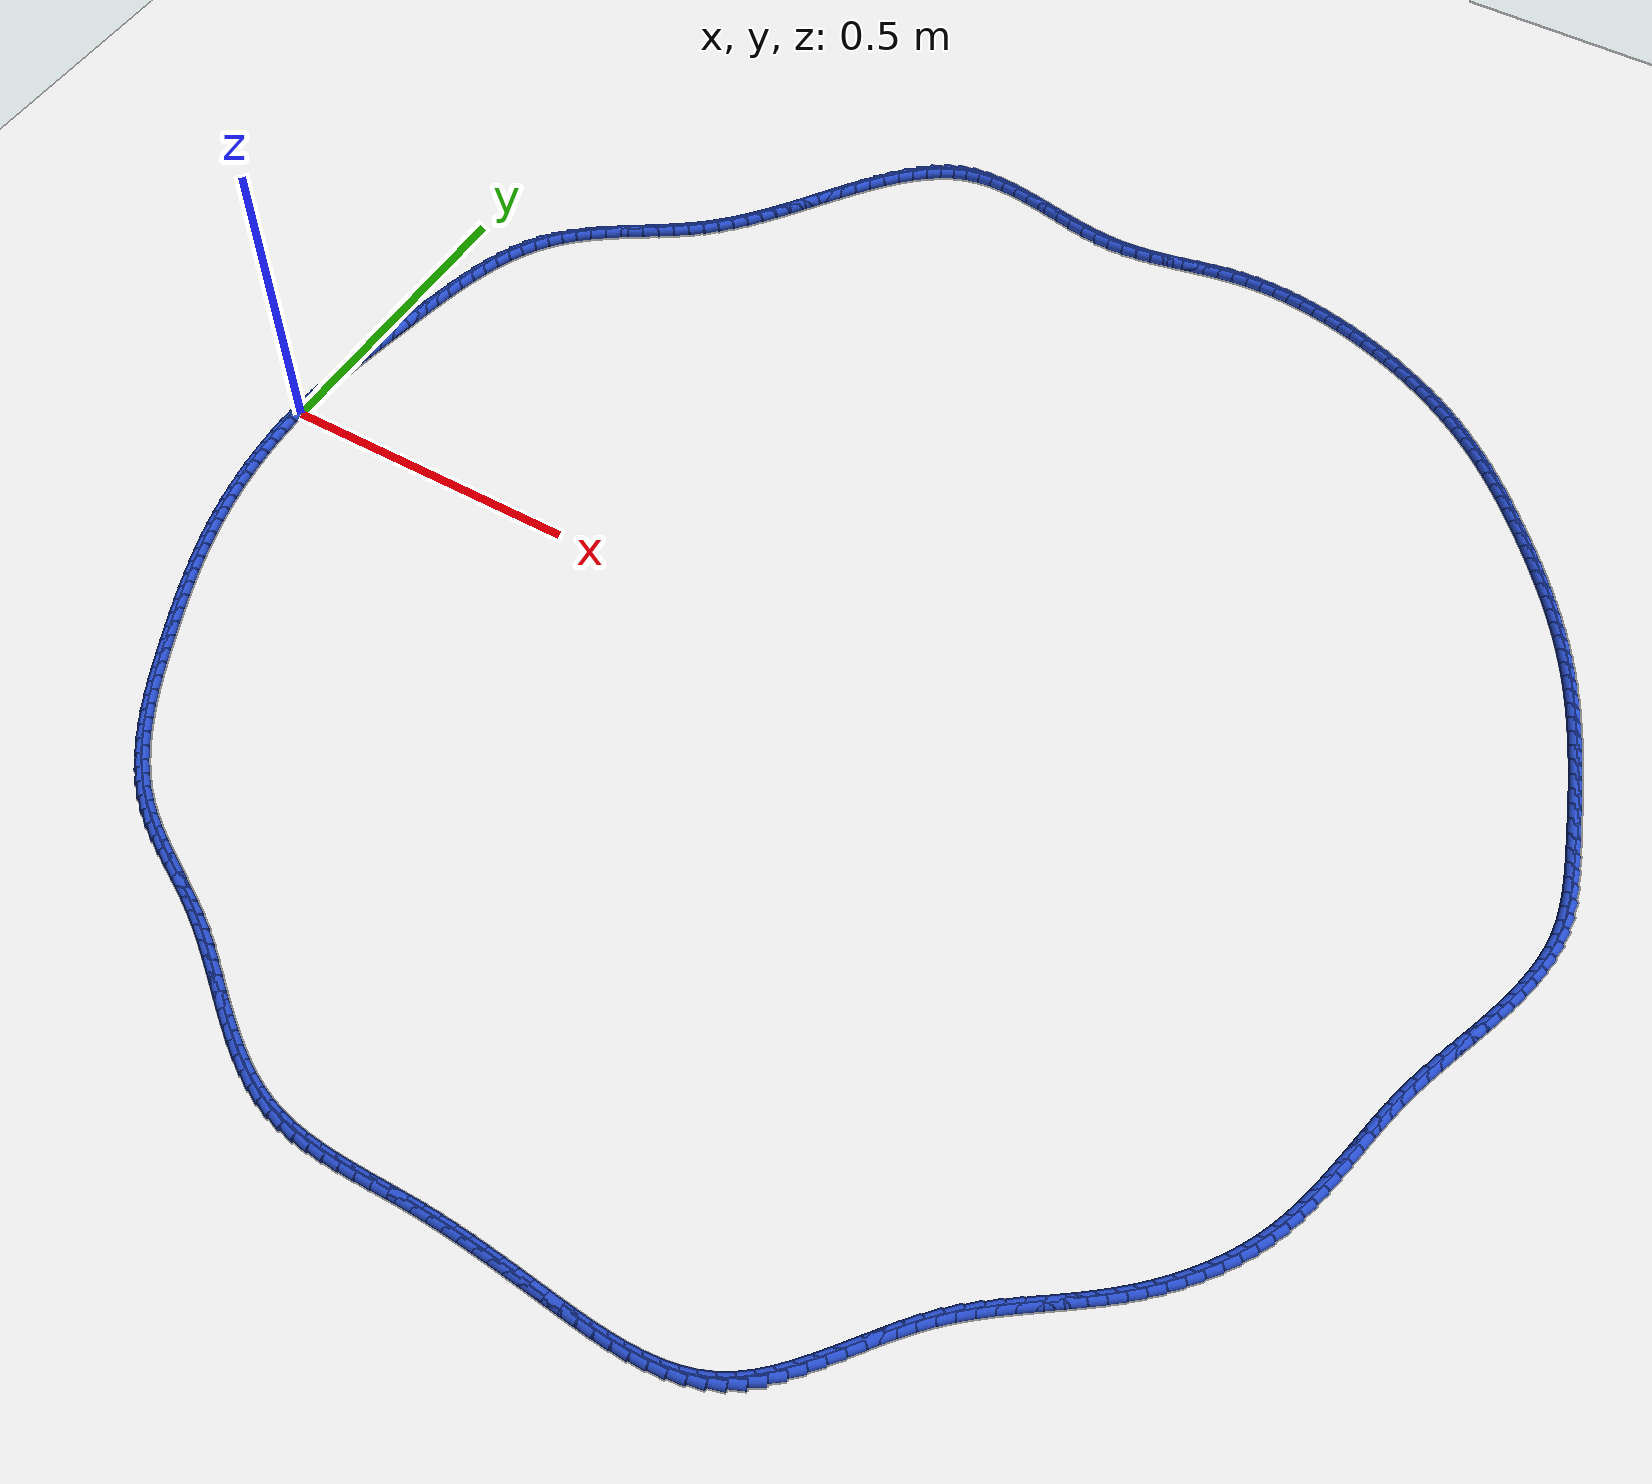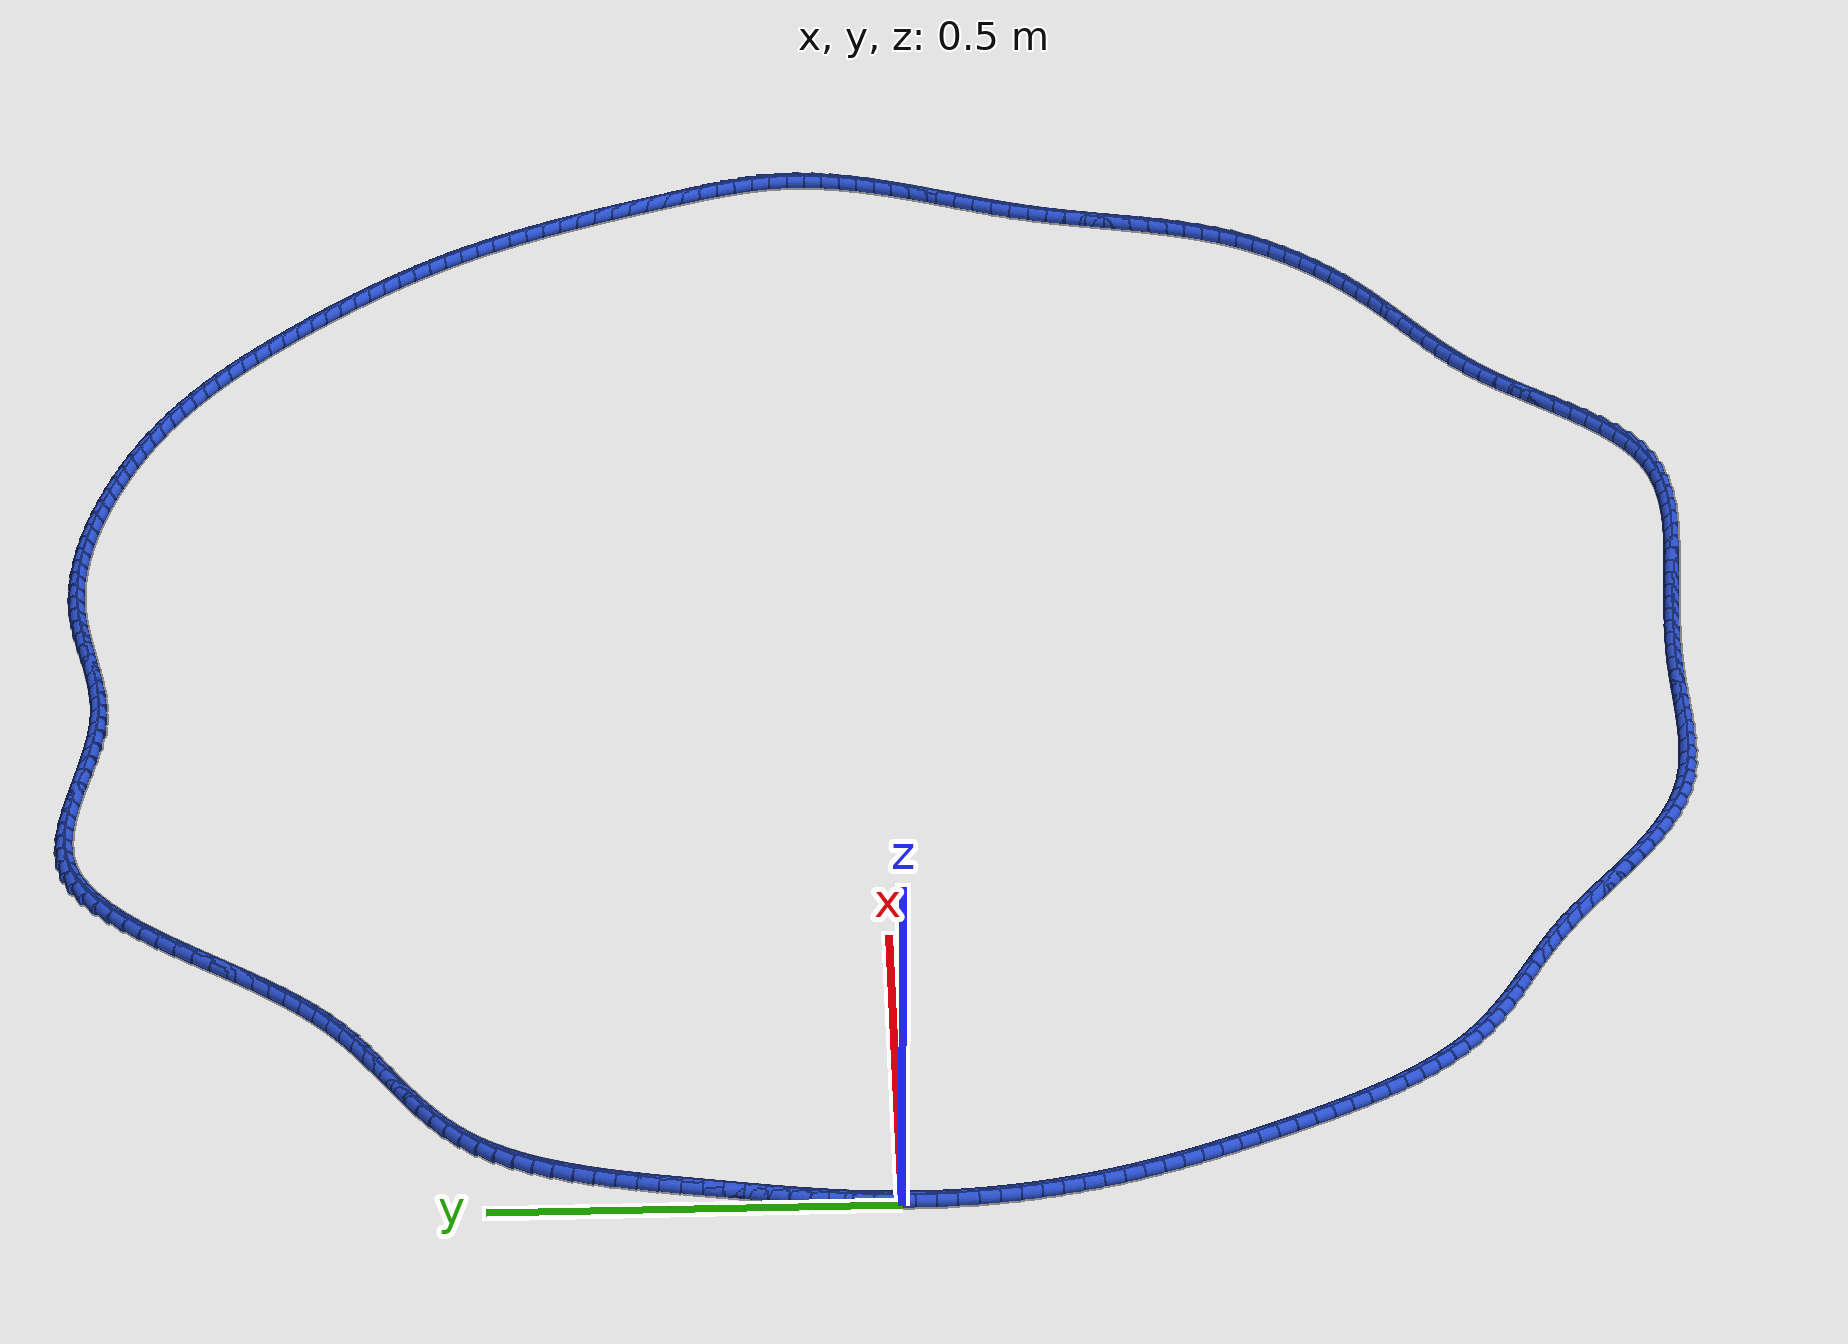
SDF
<sdf version="1.6">
 <world name="default">
  <light name="sun" type="directional">
   <pose>0 0 10 0 -0 0</pose>
   <diffuse>0.8 0.8 0.8 1</diffuse>
   <specular>0.2 0.2 0.2 1</specular>
   <attenuation>
    <range>1000</range>
    <constant>0.9</constant>
    <linear>0.01</linear>
    <quadratic>0.001</quadratic>
   </attenuation>
   <direction>-0.5 0.1 -0.9</direction>
  </light>
  <model name="ground_plane">
   <static>1</static>
   <link name="link">
    <collision name="collision">
     <geometry><plane><normal>0 0 1</normal><size>100 100</size></plane></geometry>
     <surface><friction><ode><mu>100</mu><mu2>50</mu2></ode></friction></surface>
    </collision>
    <visual name="visual">
     <cast_shadows>0</cast_shadows>
     <geometry><plane><normal>0 0 1</normal><size>100 100</size></plane></geometry>
     <material>
      <script><uri>file://media/materials/scripts/gazebo.material</uri><name>Gazebo/WhiteGlow</name></script>
     </material>
    </visual>
   </link>
  </model>
  <gravity>0 0 -9.8</gravity>
  <magnetic_field>6e-06 2.3e-05 -4.2e-05</magnetic_field>
  <atmosphere type="adiabatic"/>
  <physics name="default_physics" default="0" type="ode">
   <max_step_size>0.001</max_step_size>
   <real_time_factor>1</real_time_factor>
   <real_time_update_rate>1000</real_time_update_rate>
  </physics>
  <scene><ambient>0.4 0.4 0.4 1</ambient><background>0.7 0.7 0.7 1</background><shadows>1</shadows></scene>
  <spherical_coordinates>
   <surface_model>EARTH_WGS84</surface_model>
   <latitude_deg>0</latitude_deg>
   <longitude_deg>0</longitude_deg>
   <elevation>0</elevation>
   <heading_deg>0</heading_deg>
  </spherical_coordinates>
  <model name="line">
   <link name="link_0">
    <pose>1.214306433183765e-17 3.469446951953614e-17 0.01 0 1.57 1.5339829788960886</pose>
    <collision name="collision">
     <geometry><cylinder><radius>0.01</radius><length>0.08</length></cylinder></geometry>
    </collision>
    <visual name="visual">
     <material>
      <script><name>Gazebo/Blue</name><uri>file://media/materials/scripts/gazebo.material</uri></script>
     </material>
     <geometry><cylinder><radius>0.01</radius><length>0.08</length></cylinder></geometry>
    </visual>
   </link>
   <link name="link_1">
    <pose>0.0009274351517306487 0.025181522638676877 0.01 0 1.57 1.5053725256804775</pose>
    <collision name="collision">
     <geometry><cylinder><radius>0.01</radius><length>0.08</length></cylinder></geometry>
    </collision>
    <visual name="visual">
     <material>
      <script><name>Gazebo/Blue</name><uri>file://media/materials/scripts/gazebo.material</uri></script>
     </material>
     <geometry><cylinder><radius>0.01</radius><length>0.08</length></cylinder></geometry>
    </visual>
   </link>
   <link name="link_2">
    <pose>0.0025709081407248808 0.05026608595606695 0.01 0 1.57 1.4801818989352191</pose>
    <collision name="collision">
     <geometry><cylinder><radius>0.01</radius><length>0.08</length></cylinder></geometry>
    </collision>
    <visual name="visual">
     <material>
      <script><name>Gazebo/Blue</name><uri>file://media/materials/scripts/gazebo.material</uri></script>
     </material>
     <geometry><cylinder><radius>0.01</radius><length>0.08</length></cylinder></geometry>
    </visual>
   </link>
   <link name="link_3">
    <pose>0.004845414192400432 0.07529827333623466 0.01 0 1.57 1.458558620652903</pose>
    <collision name="collision">
     <geometry><cylinder><radius>0.01</radius><length>0.08</length></cylinder></geometry>
    </collision>
    <visual name="visual">
     <material>
      <script><name>Gazebo/Blue</name><uri>file://media/materials/scripts/gazebo.material</uri></script>
     </material>
     <geometry><cylinder><radius>0.01</radius><length>0.08</length></cylinder></geometry>
    </visual>
   </link>
   <link name="link_4">
    <pose>0.0076659485321750095 0.10032266816324444 0.01 0 1.57 1.4405952435260345</pose>
    <collision name="collision">
     <geometry><cylinder><radius>0.01</radius><length>0.08</length></cylinder></geometry>
    </collision>
    <visual name="visual">
     <material>
      <script><name>Gazebo/Blue</name><uri>file://media/materials/scripts/gazebo.material</uri></script>
     </material>
     <geometry><cylinder><radius>0.01</radius><length>0.08</length></cylinder></geometry>
    </visual>
   </link>
   <link name="link_5">
    <pose>0.01094750638546634 0.12538385382116074 0.01 0 1.57 1.426336170725187</pose>
    <collision name="collision">
     <geometry><cylinder><radius>0.01</radius><length>0.08</length></cylinder></geometry>
    </collision>
    <visual name="visual">
     <material>
      <script><name>Gazebo/Blue</name><uri>file://media/materials/scripts/gazebo.material</uri></script>
     </material>
     <geometry><cylinder><radius>0.01</radius><length>0.08</length></cylinder></geometry>
    </visual>
   </link>
   <link name="link_6">
    <pose>0.01460508297769213 0.15052641369404796 0.01 0 1.57 1.4157847231987168</pose>
    <collision name="collision">
     <geometry><cylinder><radius>0.01</radius><length>0.08</length></cylinder></geometry>
    </collision>
    <visual name="visual">
     <material>
      <script><name>Gazebo/Blue</name><uri>file://media/materials/scripts/gazebo.material</uri></script>
     </material>
     <geometry><cylinder><radius>0.01</radius><length>0.08</length></cylinder></geometry>
    </visual>
   </link>
   <link name="link_7">
    <pose>0.018553673534270104 0.17579493116597053 0.01 0 1.57 1.4089097297832713</pose>
    <collision name="collision">
     <geometry><cylinder><radius>0.01</radius><length>0.08</length></cylinder></geometry>
    </collision>
    <visual name="visual">
     <material>
      <script><name>Gazebo/Blue</name><uri>file://media/materials/scripts/gazebo.material</uri></script>
     </material>
     <geometry><cylinder><radius>0.01</radius><length>0.08</length></cylinder></geometry>
    </visual>
   </link>
   <link name="link_8">
    <pose>0.022708273280617974 0.20123398962099284 0.01 0 1.57 1.4056511756160563</pose>
    <collision name="collision">
     <geometry><cylinder><radius>0.01</radius><length>0.08</length></cylinder></geometry>
    </collision>
    <visual name="visual">
     <material>
      <script><name>Gazebo/Blue</name><uri>file://media/materials/scripts/gazebo.material</uri></script>
     </material>
     <geometry><cylinder><radius>0.01</radius><length>0.08</length></cylinder></geometry>
    </visual>
   </link>
   <link name="link_9">
    <pose>0.026983877442153456 0.22688817244317938 0.01 0 1.57 1.4056824515666588</pose>
    <collision name="collision">
     <geometry><cylinder><radius>0.01</radius><length>0.08</length></cylinder></geometry>
    </collision>
    <visual name="visual">
     <material>
      <script><name>Gazebo/Blue</name><uri>file://media/materials/scripts/gazebo.material</uri></script>
     </material>
     <geometry><cylinder><radius>0.01</radius><length>0.08</length></cylinder></geometry>
    </visual>
   </link>
   <link name="link_10">
    <pose>0.03130119356682461 0.25279762967780856 0.01 0 1.57 1.4038542729794004</pose>
    <collision name="collision">
     <geometry><cylinder><radius>0.01</radius><length>0.08</length></cylinder></geometry>
    </collision>
    <visual name="visual">
     <material>
      <script><name>Gazebo/Blue</name><uri>file://media/materials/scripts/gazebo.material</uri></script>
     </material>
     <geometry><cylinder><radius>0.01</radius><length>0.08</length></cylinder></geometry>
    </visual>
   </link>
   <link name="link_11">
    <pose>0.035701252915136025 0.2789091280258325 0.01 0 1.57 1.3953896338001182</pose>
    <collision name="collision">
     <geometry><cylinder><radius>0.01</radius><length>0.08</length></cylinder></geometry>
    </collision>
    <visual name="visual">
     <material>
      <script><name>Gazebo/Blue</name><uri>file://media/materials/scripts/gazebo.material</uri></script>
     </material>
     <geometry><cylinder><radius>0.01</radius><length>0.08</length></cylinder></geometry>
    </visual>
   </link>
   <link name="link_12">
    <pose>0.04033956917689046 0.3050805842692029 0.01 0 1.57 1.3800640167072322</pose>
    <collision name="collision">
     <geometry><cylinder><radius>0.01</radius><length>0.08</length></cylinder></geometry>
    </collision>
    <visual name="visual">
     <material>
      <script><name>Gazebo/Blue</name><uri>file://media/materials/scripts/gazebo.material</uri></script>
     </material>
     <geometry><cylinder><radius>0.01</radius><length>0.08</length></cylinder></geometry>
    </visual>
   </link>
   <link name="link_13">
    <pose>0.04537619920073838 0.3311663892400986 0.01 0 1.57 1.357679555874147</pose>
    <collision name="collision">
     <geometry><cylinder><radius>0.01</radius><length>0.08</length></cylinder></geometry>
    </collision>
    <visual name="visual">
     <material>
      <script><name>Gazebo/Blue</name><uri>file://media/materials/scripts/gazebo.material</uri></script>
     </material>
     <geometry><cylinder><radius>0.01</radius><length>0.08</length></cylinder></geometry>
    </visual>
   </link>
   <link name="link_14">
    <pose>0.050971199835330196 0.3570209337706978 0.01 0 1.57 1.327887093391454</pose>
    <collision name="collision">
     <geometry><cylinder><radius>0.01</radius><length>0.08</length></cylinder></geometry>
    </collision>
    <visual name="visual">
     <material>
      <script><name>Gazebo/Blue</name><uri>file://media/materials/scripts/gazebo.material</uri></script>
     </material>
     <geometry><cylinder><radius>0.01</radius><length>0.08</length></cylinder></geometry>
    </visual>
   </link>
   <link name="link_15">
    <pose>0.05728462792931636 0.3824986086931794 0.01 0 1.57 1.2902065460829704</pose>
    <collision name="collision">
     <geometry><cylinder><radius>0.01</radius><length>0.08</length></cylinder></geometry>
    </collision>
    <visual name="visual">
     <material>
      <script><name>Gazebo/Blue</name><uri>file://media/materials/scripts/gazebo.material</uri></script>
     </material>
     <geometry><cylinder><radius>0.01</radius><length>0.08</length></cylinder></geometry>
    </visual>
   </link>
   <link name="link_16">
    <pose>0.0644765403313473 0.40745380483972193 0.01 0 1.57 1.2440606908791365</pose>
    <collision name="collision">
     <geometry><cylinder><radius>0.01</radius><length>0.08</length></cylinder></geometry>
    </collision>
    <visual name="visual">
     <material>
      <script><name>Gazebo/Blue</name><uri>file://media/materials/scripts/gazebo.material</uri></script>
     </material>
     <geometry><cylinder><radius>0.01</radius><length>0.08</length></cylinder></geometry>
    </visual>
   </link>
   <link name="link_17">
    <pose>0.07270699389007342 0.43174091304250384 0.01 0 1.57 1.1888332767766767</pose>
    <collision name="collision">
     <geometry><cylinder><radius>0.01</radius><length>0.08</length></cylinder></geometry>
    </collision>
    <visual name="visual">
     <material>
      <script><name>Gazebo/Blue</name><uri>file://media/materials/scripts/gazebo.material</uri></script>
     </material>
     <geometry><cylinder><radius>0.01</radius><length>0.08</length></cylinder></geometry>
    </visual>
   </link>
   <link name="link_18">
    <pose>0.0821360454541452 0.455214324133704 0.01 0 1.57 1.1239647724169817</pose>
    <collision name="collision">
     <geometry><cylinder><radius>0.01</radius><length>0.08</length></cylinder></geometry>
    </collision>
    <visual name="visual">
     <material>
      <script><name>Gazebo/Blue</name><uri>file://media/materials/scripts/gazebo.material</uri></script>
     </material>
     <geometry><cylinder><radius>0.01</radius><length>0.08</length></cylinder></geometry>
    </visual>
   </link>
   <link name="link_19">
    <pose>0.09292375187221302 0.4777284289455006 0.01 0 1.57 1.0490977574368707</pose>
    <collision name="collision">
     <geometry><cylinder><radius>0.01</radius><length>0.08</length></cylinder></geometry>
    </collision>
    <visual name="visual">
     <material>
      <script><name>Gazebo/Blue</name><uri>file://media/materials/scripts/gazebo.material</uri></script>
     </material>
     <geometry><cylinder><radius>0.01</radius><length>0.08</length></cylinder></geometry>
    </visual>
   </link>
   <link name="link_20">
    <pose>0.10523016999292738 0.49913761831007253 0.01 0 1.57 0.9642735368970907</pose>
    <collision name="collision">
     <geometry><cylinder><radius>0.01</radius><length>0.08</length></cylinder></geometry>
    </collision>
    <visual name="visual">
     <material>
      <script><name>Gazebo/Blue</name><uri>file://media/materials/scripts/gazebo.material</uri></script>
     </material>
     <geometry><cylinder><radius>0.01</radius><length>0.08</length></cylinder></geometry>
    </visual>
   </link>
   <link name="link_21">
    <pose>0.11921535666493863 0.5192962830595982 0.01 0 1.57 0.8706599605848814</pose>
    <collision name="collision">
     <geometry><cylinder><radius>0.01</radius><length>0.08</length></cylinder></geometry>
    </collision>
    <visual name="visual">
     <material>
      <script><name>Gazebo/Blue</name><uri>file://media/materials/scripts/gazebo.material</uri></script>
     </material>
     <geometry><cylinder><radius>0.01</radius><length>0.08</length></cylinder></geometry>
    </visual>
   </link>
   <link name="link_22">
    <pose>0.13502980089519595 0.5380666573283572 0.01 0 1.57 0.7814361946580123</pose>
    <collision name="collision">
     <geometry><cylinder><radius>0.01</radius><length>0.08</length></cylinder></geometry>
    </collision>
    <visual name="visual">
     <material>
      <script><name>Gazebo/Blue</name><uri>file://media/materials/scripts/gazebo.material</uri></script>
     </material>
     <geometry><cylinder><radius>0.01</radius><length>0.08</length></cylinder></geometry>
    </visual>
   </link>
   <link name="link_23">
    <pose>0.15259802079737098 0.5554962163987637 0.01 0 1.57 0.7093450802969794</pose>
    <collision name="collision">
     <geometry><cylinder><radius>0.01</radius><length>0.08</length></cylinder></geometry>
    </collision>
    <visual name="visual">
     <material>
      <script><name>Gazebo/Blue</name><uri>file://media/materials/scripts/gazebo.material</uri></script>
     </material>
     <geometry><cylinder><radius>0.01</radius><length>0.08</length></cylinder></geometry>
    </visual>
   </link>
   <link name="link_24">
    <pose>0.17161523035400042 0.571820409145351 0.01 0 1.57 0.6545022769537067</pose>
    <collision name="collision">
     <geometry><cylinder><radius>0.01</radius><length>0.08</length></cylinder></geometry>
    </collision>
    <visual name="visual">
     <material>
      <script><name>Gazebo/Blue</name><uri>file://media/materials/scripts/gazebo.material</uri></script>
     </material>
     <geometry><cylinder><radius>0.01</radius><length>0.08</length></cylinder></geometry>
    </visual>
   </link>
   <link name="link_25">
    <pose>0.19176640901353828 0.5872830742702827 0.01 0 1.57 0.6160154124690302</pose>
    <collision name="collision">
     <geometry><cylinder><radius>0.01</radius><length>0.08</length></cylinder></geometry>
    </collision>
    <visual name="visual">
     <material>
      <script><name>Gazebo/Blue</name><uri>file://media/materials/scripts/gazebo.material</uri></script>
     </material>
     <geometry><cylinder><radius>0.01</radius><length>0.08</length></cylinder></geometry>
    </visual>
   </link>
   <link name="link_26">
    <pose>0.2127365362244386 0.6021280504757226 0.01 0 1.57 0.5929859120009084</pose>
    <collision name="collision">
     <geometry><cylinder><radius>0.01</radius><length>0.08</length></cylinder></geometry>
    </collision>
    <visual name="visual">
     <material>
      <script><name>Gazebo/Blue</name><uri>file://media/materials/scripts/gazebo.material</uri></script>
     </material>
     <geometry><cylinder><radius>0.01</radius><length>0.08</length></cylinder></geometry>
    </visual>
   </link>
   <link name="link_27">
    <pose>0.23421059143515535 0.6165991764638342 0.01 0 1.57 0.584772356523271</pose>
    <collision name="collision">
     <geometry><cylinder><radius>0.01</radius><length>0.08</length></cylinder></geometry>
    </collision>
    <visual name="visual">
     <material>
      <script><name>Gazebo/Blue</name><uri>file://media/materials/scripts/gazebo.material</uri></script>
     </material>
     <geometry><cylinder><radius>0.01</radius><length>0.08</length></cylinder></geometry>
    </visual>
   </link>
   <link name="link_28">
    <pose>0.2558735540941427 0.6309402909367814 0.01 0 1.57 0.5911155588862479</pose>
    <collision name="collision">
     <geometry><cylinder><radius>0.01</radius><length>0.08</length></cylinder></geometry>
    </collision>
    <visual name="visual">
     <material>
      <script><name>Gazebo/Blue</name><uri>file://media/materials/scripts/gazebo.material</uri></script>
     </material>
     <geometry><cylinder><radius>0.01</radius><length>0.08</length></cylinder></geometry>
    </visual>
   </link>
   <link name="link_29">
    <pose>0.2774104036498544 0.6453952325967274 0.01 0 1.57 0.6121754178002337</pose>
    <collision name="collision">
     <geometry><cylinder><radius>0.01</radius><length>0.08</length></cylinder></geometry>
    </collision>
    <visual name="visual">
     <material>
      <script><name>Gazebo/Blue</name><uri>file://media/materials/scripts/gazebo.material</uri></script>
     </material>
     <geometry><cylinder><radius>0.01</radius><length>0.08</length></cylinder></geometry>
    </visual>
   </link>
   <link name="link_30">
    <pose>0.29850611955074474 0.6602078401458363 0.01 0 1.57 0.648499190710735</pose>
    <collision name="collision">
     <geometry><cylinder><radius>0.01</radius><length>0.08</length></cylinder></geometry>
    </collision>
    <visual name="visual">
     <material>
      <script><name>Gazebo/Blue</name><uri>file://media/materials/scripts/gazebo.material</uri></script>
     </material>
     <geometry><cylinder><radius>0.01</radius><length>0.08</length></cylinder></geometry>
    </visual>
   </link>
   <link name="link_31">
    <pose>0.3188456812452676 0.6756219522862716 0.01 0 1.57 0.7005443801936809</pose>
    <collision name="collision">
     <geometry><cylinder><radius>0.01</radius><length>0.08</length></cylinder></geometry>
    </collision>
    <visual name="visual">
     <material>
      <script><name>Gazebo/Blue</name><uri>file://media/materials/scripts/gazebo.material</uri></script>
     </material>
     <geometry><cylinder><radius>0.01</radius><length>0.08</length></cylinder></geometry>
    </visual>
   </link>
   <link name="link_32">
    <pose>0.3381222324329792 0.6918763141746251 0.01 0 1.57 0.7586901255743843</pose>
    <collision name="collision">
     <geometry><cylinder><radius>0.01</radius><length>0.08</length></cylinder></geometry>
    </collision>
    <visual name="visual">
     <material>
      <script><name>Gazebo/Blue</name><uri>file://media/materials/scripts/gazebo.material</uri></script>
     </material>
     <geometry><cylinder><radius>0.01</radius><length>0.08</length></cylinder></geometry>
    </visual>
   </link>
   <link name="link_33">
    <pose>0.3562569998123229 0.7090673736355638 0.01 0 1.57 0.8109117768195722</pose>
    <collision name="collision">
     <geometry><cylinder><radius>0.01</radius><length>0.08</length></cylinder></geometry>
    </collision>
    <visual name="visual">
     <material>
      <script><name>Gazebo/Blue</name><uri>file://media/materials/scripts/gazebo.material</uri></script>
     </material>
     <geometry><cylinder><radius>0.01</radius><length>0.08</length></cylinder></geometry>
    </visual>
   </link>
   <link name="link_34">
    <pose>0.37342422299148 0.727133727789522 0.01 0 1.57 0.8557585079516992</pose>
    <collision name="collision">
     <geometry><cylinder><radius>0.01</radius><length>0.08</length></cylinder></geometry>
    </collision>
    <visual name="visual">
     <material>
      <script><name>Gazebo/Blue</name><uri>file://media/materials/scripts/gazebo.material</uri></script>
     </material>
     <geometry><cylinder><radius>0.01</radius><length>0.08</length></cylinder></geometry>
    </visual>
   </link>
   <link name="link_35">
    <pose>0.3898113086360143 0.7460057590406061 0.01 0 1.57 0.892709546757612</pose>
    <collision name="collision">
     <geometry><cylinder><radius>0.01</radius><length>0.08</length></cylinder></geometry>
    </collision>
    <visual name="visual">
     <material>
      <script><name>Gazebo/Blue</name><uri>file://media/materials/scripts/gazebo.material</uri></script>
     </material>
     <geometry><cylinder><radius>0.01</radius><length>0.08</length></cylinder></geometry>
    </visual>
   </link>
   <link name="link_36">
    <pose>0.4056056634114896 0.765613849792922 0.01 0 1.57 0.9215393939670298</pose>
    <collision name="collision">
     <geometry><cylinder><radius>0.01</radius><length>0.08</length></cylinder></geometry>
    </collision>
    <visual name="visual">
     <material>
      <script><name>Gazebo/Blue</name><uri>file://media/materials/scripts/gazebo.material</uri></script>
     </material>
     <geometry><cylinder><radius>0.01</radius><length>0.08</length></cylinder></geometry>
    </visual>
   </link>
   <link name="link_37">
    <pose>0.4209946939834701 0.7858883824505769 0.01 0 1.57 0.9422525304581245</pose>
    <collision name="collision">
     <geometry><cylinder><radius>0.01</radius><length>0.08</length></cylinder></geometry>
    </collision>
    <visual name="visual">
     <material>
      <script><name>Gazebo/Blue</name><uri>file://media/materials/scripts/gazebo.material</uri></script>
     </material>
     <geometry><cylinder><radius>0.01</radius><length>0.08</length></cylinder></geometry>
    </visual>
   </link>
   <link name="link_38">
    <pose>0.43616580701751995 0.8067597394176774 0.01 0 1.57 0.9550196924728335</pose>
    <collision name="collision">
     <geometry><cylinder><radius>0.01</radius><length>0.08</length></cylinder></geometry>
    </collision>
    <visual name="visual">
     <material>
      <script><name>Gazebo/Blue</name><uri>file://media/materials/scripts/gazebo.material</uri></script>
     </material>
     <geometry><cylinder><radius>0.01</radius><length>0.08</length></cylinder></geometry>
    </visual>
   </link>
   <link name="link_39">
    <pose>0.45130640917920295 0.8281583030983296 0.01 0 1.57 0.9601259022935649</pose>
    <collision name="collision">
     <geometry><cylinder><radius>0.01</radius><length>0.08</length></cylinder></geometry>
    </collision>
    <visual name="visual">
     <material>
      <script><name>Gazebo/Blue</name><uri>file://media/materials/scripts/gazebo.material</uri></script>
     </material>
     <geometry><cylinder><radius>0.01</radius><length>0.08</length></cylinder></geometry>
    </visual>
   </link>
   <link name="link_40">
    <pose>0.46660390667654905 0.850014454698993 0.01 0 1.57 0.9573834057649223</pose>
    <collision name="collision">
     <geometry><cylinder><radius>0.01</radius><length>0.08</length></cylinder></geometry>
    </collision>
    <visual name="visual">
     <material>
      <script><name>Gazebo/Blue</name><uri>file://media/materials/scripts/gazebo.material</uri></script>
     </material>
     <geometry><cylinder><radius>0.01</radius><length>0.08</length></cylinder></geometry>
    </visual>
   </link>
   <link name="link_41">
    <pose>0.4822239821156335 0.8722017114166074 0.01 0 1.57 0.9450894593575524</pose>
    <collision name="collision">
     <geometry><cylinder><radius>0.01</radius><length>0.08</length></cylinder></geometry>
    </collision>
    <visual name="visual">
     <material>
      <script><name>Gazebo/Blue</name><uri>file://media/materials/scripts/gazebo.material</uri></script>
     </material>
     <geometry><cylinder><radius>0.01</radius><length>0.08</length></cylinder></geometry>
    </visual>
   </link>
   <link name="link_42">
    <pose>0.49825251416043354 0.8943846945139798 0.01 0 1.57 0.9226713528026133</pose>
    <collision name="collision">
     <geometry><cylinder><radius>0.01</radius><length>0.08</length></cylinder></geometry>
    </collision>
    <visual name="visual">
     <material>
      <script><name>Gazebo/Blue</name><uri>file://media/materials/scripts/gazebo.material</uri></script>
     </material>
     <geometry><cylinder><radius>0.01</radius><length>0.08</length></cylinder></geometry>
    </visual>
   </link>
   <link name="link_43">
    <pose>0.5147570606275476 0.9161800683431847 0.01 0 1.57 0.8894612419853342</pose>
    <collision name="collision">
     <geometry><cylinder><radius>0.01</radius><length>0.08</length></cylinder></geometry>
    </collision>
    <visual name="visual">
     <material>
      <script><name>Gazebo/Blue</name><uri>file://media/materials/scripts/gazebo.material</uri></script>
     </material>
     <geometry><cylinder><radius>0.01</radius><length>0.08</length></cylinder></geometry>
    </visual>
   </link>
   <link name="link_44">
    <pose>0.5318051793335732 0.9372044972562946 0.01 0 1.57 0.844241294685128</pose>
    <collision name="collision">
     <geometry><cylinder><radius>0.01</radius><length>0.08</length></cylinder></geometry>
    </collision>
    <visual name="visual">
     <material>
      <script><name>Gazebo/Blue</name><uri>file://media/materials/scripts/gazebo.material</uri></script>
     </material>
     <geometry><cylinder><radius>0.01</radius><length>0.08</length></cylinder></geometry>
    </visual>
   </link>
   <link name="link_45">
    <pose>0.549464428095109 0.957074645605384 0.01 0 1.57 0.7852507833217689</pose>
    <collision name="collision">
     <geometry><cylinder><radius>0.01</radius><length>0.08</length></cylinder></geometry>
    </collision>
    <visual name="visual">
     <material>
      <script><name>Gazebo/Blue</name><uri>file://media/materials/scripts/gazebo.material</uri></script>
     </material>
     <geometry><cylinder><radius>0.01</radius><length>0.08</length></cylinder></geometry>
    </visual>
   </link>
   <link name="link_46">
    <pose>0.567802364728753 0.9754071777425263 0.01 0 1.57 0.7102464121352884</pose>
    <collision name="collision">
     <geometry><cylinder><radius>0.01</radius><length>0.08</length></cylinder></geometry>
    </collision>
    <visual name="visual">
     <material>
      <script><name>Gazebo/Blue</name><uri>file://media/materials/scripts/gazebo.material</uri></script>
     </material>
     <geometry><cylinder><radius>0.01</radius><length>0.08</length></cylinder></geometry>
    </visual>
   </link>
   <link name="link_47">
    <pose>0.5868865470511038 0.9918187580197952 0.01 0 1.57 0.6167280467926436</pose>
    <collision name="collision">
     <geometry><cylinder><radius>0.01</radius><length>0.08</length></cylinder></geometry>
    </collision>
    <visual name="visual">
     <material>
      <script><name>Gazebo/Blue</name><uri>file://media/materials/scripts/gazebo.material</uri></script>
     </material>
     <geometry><cylinder><radius>0.01</radius><length>0.08</length></cylinder></geometry>
    </visual>
   </link>
   <link name="link_48">
    <pose>0.6067845328787589 1.0059260507892642 0.01 0 1.57 0.5025116786537385</pose>
    <collision name="collision">
     <geometry><cylinder><radius>0.01</radius><length>0.08</length></cylinder></geometry>
    </collision>
    <visual name="visual">
     <material>
      <script><name>Gazebo/Blue</name><uri>file://media/materials/scripts/gazebo.material</uri></script>
     </material>
     <geometry><cylinder><radius>0.01</radius><length>0.08</length></cylinder></geometry>
    </visual>
   </link>
   <link name="link_49">
    <pose>0.6275638800283165 1.0173457204030067 0.01 0 1.57 0.366870027957161</pose>
    <collision name="collision">
     <geometry><cylinder><radius>0.01</radius><length>0.08</length></cylinder></geometry>
    </collision>
    <visual name="visual">
     <material>
      <script><name>Gazebo/Blue</name><uri>file://media/materials/scripts/gazebo.material</uri></script>
     </material>
     <geometry><cylinder><radius>0.01</radius><length>0.08</length></cylinder></geometry>
    </visual>
   </link>
   <link name="link_50">
    <pose>0.6492919999099732 1.025695112844641 0.01 0 1.57 0.22182237832166485</pose>
    <collision name="collision">
     <geometry><cylinder><radius>0.01</radius><length>0.08</length></cylinder></geometry>
    </collision>
    <visual name="visual">
     <material>
      <script><name>Gazebo/Blue</name><uri>file://media/materials/scripts/gazebo.material</uri></script>
     </material>
     <geometry><cylinder><radius>0.01</radius><length>0.08</length></cylinder></geometry>
    </visual>
   </link>
   <link name="link_51">
    <pose>0.6719885406655574 1.0308139479143286 0.01 0 1.57 0.09598922127501763</pose>
    <collision name="collision">
     <geometry><cylinder><radius>0.01</radius><length>0.08</length></cylinder></geometry>
    </collision>
    <visual name="visual">
     <material>
      <script><name>Gazebo/Blue</name><uri>file://media/materials/scripts/gazebo.material</uri></script>
     </material>
     <geometry><cylinder><radius>0.01</radius><length>0.08</length></cylinder></geometry>
    </visual>
   </link>
   <link name="link_52">
    <pose>0.6955568890585775 1.0330832292752663 0.01 0 1.57 -0.004870464921037287</pose>
    <collision name="collision">
     <geometry><cylinder><radius>0.01</radius><length>0.08</length></cylinder></geometry>
    </collision>
    <visual name="visual">
     <material>
      <script><name>Gazebo/Blue</name><uri>file://media/materials/scripts/gazebo.material</uri></script>
     </material>
     <geometry><cylinder><radius>0.01</radius><length>0.08</length></cylinder></geometry>
    </visual>
   </link>
   <link name="link_53">
    <pose>0.7198830795682591 1.0329647484808804 0.01 0 1.57 -0.08169386236797921</pose>
    <collision name="collision">
     <geometry><cylinder><radius>0.01</radius><length>0.08</length></cylinder></geometry>
    </collision>
    <visual name="visual">
     <material>
      <script><name>Gazebo/Blue</name><uri>file://media/materials/scripts/gazebo.material</uri></script>
     </material>
     <geometry><cylinder><radius>0.01</radius><length>0.08</length></cylinder></geometry>
    </visual>
   </link>
   <link name="link_54">
    <pose>0.7448531466738287 1.0309202970845976 0.01 0 1.57 -0.13673489549262136</pose>
    <collision name="collision">
     <geometry><cylinder><radius>0.01</radius><length>0.08</length></cylinder></geometry>
    </collision>
    <visual name="visual">
     <material>
      <script><name>Gazebo/Blue</name><uri>file://media/materials/scripts/gazebo.material</uri></script>
     </material>
     <geometry><cylinder><radius>0.01</radius><length>0.08</length></cylinder></geometry>
    </visual>
   </link>
   <link name="link_55">
    <pose>0.7703531248545111 1.0274116666398443 0.01 0 1.57 -0.1723369082654439</pose>
    <collision name="collision">
     <geometry><cylinder><radius>0.01</radius><length>0.08</length></cylinder></geometry>
    </collision>
    <visual name="visual">
     <material>
      <script><name>Gazebo/Blue</name><uri>file://media/materials/scripts/gazebo.material</uri></script>
     </material>
     <geometry><cylinder><radius>0.01</radius><length>0.08</length></cylinder></geometry>
    </visual>
   </link>
   <link name="link_56">
    <pose>0.7962690485895317 1.022900648700047 0.01 0 1.57 -0.1903453874338346</pose>
    <collision name="collision">
     <geometry><cylinder><radius>0.01</radius><length>0.08</length></cylinder></geometry>
    </collision>
    <visual name="visual">
     <material>
      <script><name>Gazebo/Blue</name><uri>file://media/materials/scripts/gazebo.material</uri></script>
     </material>
     <geometry><cylinder><radius>0.01</radius><length>0.08</length></cylinder></geometry>
    </visual>
   </link>
   <link name="link_57">
    <pose>0.8224869523581163 1.0178490348186318 0.01 0 1.57 -0.19189964784672442</pose>
    <collision name="collision">
     <geometry><cylinder><radius>0.01</radius><length>0.08</length></cylinder></geometry>
    </collision>
    <visual name="visual">
     <material>
      <script><name>Gazebo/Blue</name><uri>file://media/materials/scripts/gazebo.material</uri></script>
     </material>
     <geometry><cylinder><radius>0.01</radius><length>0.08</length></cylinder></geometry>
    </visual>
   </link>
   <link name="link_58">
    <pose>0.8488928706394905 1.0127186165490254 0.01 0 1.57 -0.1773991996072403</pose>
    <collision name="collision">
     <geometry><cylinder><radius>0.01</radius><length>0.08</length></cylinder></geometry>
    </collision>
    <visual name="visual">
     <material>
      <script><name>Gazebo/Blue</name><uri>file://media/materials/scripts/gazebo.material</uri></script>
     </material>
     <geometry><cylinder><radius>0.01</radius><length>0.08</length></cylinder></geometry>
    </visual>
   </link>
   <link name="link_59">
    <pose>0.8753728379128798 1.007971185444654 0.01 0 1.57 -0.14654567163250834</pose>
    <collision name="collision">
     <geometry><cylinder><radius>0.01</radius><length>0.08</length></cylinder></geometry>
    </collision>
    <visual name="visual">
     <material>
      <script><name>Gazebo/Blue</name><uri>file://media/materials/scripts/gazebo.material</uri></script>
     </material>
     <geometry><cylinder><radius>0.01</radius><length>0.08</length></cylinder></geometry>
    </visual>
   </link>
   <link name="link_60">
    <pose>0.9018128886575095 1.0040685330589447 0.01 0 1.57 -0.09844304362267217</pose>
    <collision name="collision">
     <geometry><cylinder><radius>0.01</radius><length>0.08</length></cylinder></geometry>
    </collision>
    <visual name="visual">
     <material>
      <script><name>Gazebo/Blue</name><uri>file://media/materials/scripts/gazebo.material</uri></script>
     </material>
     <geometry><cylinder><radius>0.01</radius><length>0.08</length></cylinder></geometry>
    </visual>
   </link>
   <link name="link_61">
    <pose>0.9280990573526052 1.001472450945323 0.01 0 1.57 -0.03183169925833834</pose>
    <collision name="collision">
     <geometry><cylinder><radius>0.01</radius><length>0.08</length></cylinder></geometry>
    </collision>
    <visual name="visual">
     <material>
      <script><name>Gazebo/Blue</name><uri>file://media/materials/scripts/gazebo.material</uri></script>
     </material>
     <geometry><cylinder><radius>0.01</radius><length>0.08</length></cylinder></geometry>
    </visual>
   </link>
   <link name="link_62">
    <pose>0.954117533118761 1.0006439588054954 0.01 0 1.57 0.0453374783966986</pose>
    <collision name="collision">
     <geometry><cylinder><radius>0.01</radius><length>0.08</length></cylinder></geometry>
    </collision>
    <visual name="visual">
     <material>
      <script><name>Gazebo/Blue</name><uri>file://media/materials/scripts/gazebo.material</uri></script>
     </material>
     <geometry><cylinder><radius>0.01</radius><length>0.08</length></cylinder></geometry>
    </visual>
   </link>
   <link name="link_63">
    <pose>0.9798015615392556 1.0018092063823039 0.01 0 1.57 0.11062189219753174</pose>
    <collision name="collision">
     <geometry><cylinder><radius>0.01</radius><length>0.08</length></cylinder></geometry>
    </collision>
    <visual name="visual">
     <material>
      <script><name>Gazebo/Blue</name><uri>file://media/materials/scripts/gazebo.material</uri></script>
     </material>
     <geometry><cylinder><radius>0.01</radius><length>0.08</length></cylinder></geometry>
    </visual>
   </link>
   <link name="link_64">
    <pose>1.0051974424897039 1.0046300626487683 0.01 0 1.57 0.15974053405140326</pose>
    <collision name="collision">
     <geometry><cylinder><radius>0.01</radius><length>0.08</length></cylinder></geometry>
    </collision>
    <visual name="visual">
     <material>
      <script><name>Gazebo/Blue</name><uri>file://media/materials/scripts/gazebo.material</uri></script>
     </material>
     <geometry><cylinder><radius>0.01</radius><length>0.08</length></cylinder></geometry>
    </visual>
   </link>
   <link name="link_65">
    <pose>1.0303681062951158 1.0086853900631263 0.01 0 1.57 0.1922761442711783</pose>
    <collision name="collision">
     <geometry><cylinder><radius>0.01</radius><length>0.08</length></cylinder></geometry>
    </collision>
    <visual name="visual">
     <material>
      <script><name>Gazebo/Blue</name><uri>file://media/materials/scripts/gazebo.material</uri></script>
     </material>
     <geometry><cylinder><radius>0.01</radius><length>0.08</length></cylinder></geometry>
    </visual>
   </link>
   <link name="link_66">
    <pose>1.0553764832805026 1.0135540510836174 0.01 0 1.57 0.20814399703539768</pose>
    <collision name="collision">
     <geometry><cylinder><radius>0.01</radius><length>0.08</length></cylinder></geometry>
    </collision>
    <visual name="visual">
     <material>
      <script><name>Gazebo/Blue</name><uri>file://media/materials/scripts/gazebo.material</uri></script>
     </material>
     <geometry><cylinder><radius>0.01</radius><length>0.08</length></cylinder></geometry>
    </visual>
   </link>
   <link name="link_67">
    <pose>1.080285503770874 1.01881490816848 0.01 0 1.57 0.20732605509735863</pose>
    <collision name="collision">
     <geometry><cylinder><radius>0.01</radius><length>0.08</length></cylinder></geometry>
    </collision>
    <visual name="visual">
     <material>
      <script><name>Gazebo/Blue</name><uri>file://media/materials/scripts/gazebo.material</uri></script>
     </material>
     <geometry><cylinder><radius>0.01</radius><length>0.08</length></cylinder></geometry>
    </visual>
   </link>
   <link name="link_68">
    <pose>1.1051580980912403 1.0240468237759521 0.01 0 1.57 0.18973840762749705</pose>
    <collision name="collision">
     <geometry><cylinder><radius>0.01</radius><length>0.08</length></cylinder></geometry>
    </collision>
    <visual name="visual">
     <material>
      <script><name>Gazebo/Blue</name><uri>file://media/materials/scripts/gazebo.material</uri></script>
     </material>
     <geometry><cylinder><radius>0.01</radius><length>0.08</length></cylinder></geometry>
    </visual>
   </link>
   <link name="link_69">
    <pose>1.130057196566612 1.028828660364273 0.01 0 1.57 0.15523743946890642</pose>
    <collision name="collision">
     <geometry><cylinder><radius>0.01</radius><length>0.08</length></cylinder></geometry>
    </collision>
    <visual name="visual">
     <material>
      <script><name>Gazebo/Blue</name><uri>file://media/materials/scripts/gazebo.material</uri></script>
     </material>
     <geometry><cylinder><radius>0.01</radius><length>0.08</length></cylinder></geometry>
    </visual>
   </link>
   <link name="link_70">
    <pose>1.1550457295219996 1.0327392803916808 0.01 0 1.57 0.10423539342205594</pose>
    <collision name="collision">
     <geometry><cylinder><radius>0.01</radius><length>0.08</length></cylinder></geometry>
    </collision>
    <visual name="visual">
     <material>
      <script><name>Gazebo/Blue</name><uri>file://media/materials/scripts/gazebo.material</uri></script>
     </material>
     <geometry><cylinder><radius>0.01</radius><length>0.08</length></cylinder></geometry>
    </visual>
   </link>
   <link name="link_71">
    <pose>1.1801839685223334 1.0353691058962753 0.01 0 1.57 0.04680823275927001</pose>
    <collision name="collision">
     <geometry><cylinder><radius>0.01</radius><length>0.08</length></cylinder></geometry>
    </collision>
    <visual name="visual">
     <material>
      <script><name>Gazebo/Blue</name><uri>file://media/materials/scripts/gazebo.material</uri></script>
     </material>
     <geometry><cylinder><radius>0.01</radius><length>0.08</length></cylinder></geometry>
    </visual>
   </link>
   <link name="link_72">
    <pose>1.2054757702421408 1.0365538358164479 0.01 0 1.57 -0.00749387108331185</pose>
    <collision name="collision">
     <geometry><cylinder><radius>0.01</radius><length>0.08</length></cylinder></geometry>
    </collision>
    <visual name="visual">
     <material>
      <script><name>Gazebo/Blue</name><uri>file://media/materials/scripts/gazebo.material</uri></script>
     </material>
     <geometry><cylinder><radius>0.01</radius><length>0.08</length></cylinder></geometry>
    </visual>
   </link>
   <link name="link_73">
    <pose>1.2308710888046293 1.0363635230104722 0.01 0 1.57 -0.05832770067650977</pose>
    <collision name="collision">
     <geometry><cylinder><radius>0.01</radius><length>0.08</length></cylinder></geometry>
    </collision>
    <visual name="visual">
     <material>
      <script><name>Gazebo/Blue</name><uri>file://media/materials/scripts/gazebo.material</uri></script>
     </material>
     <geometry><cylinder><radius>0.01</radius><length>0.08</length></cylinder></geometry>
    </visual>
   </link>
   <link name="link_74">
    <pose>1.2563177223676514 1.034877593899085 0.01 0 1.57 -0.10579490099353038</pose>
    <collision name="collision">
     <geometry><cylinder><radius>0.01</radius><length>0.08</length></cylinder></geometry>
    </collision>
    <visual name="visual">
     <material>
      <script><name>Gazebo/Blue</name><uri>file://media/materials/scripts/gazebo.material</uri></script>
     </material>
     <geometry><cylinder><radius>0.01</radius><length>0.08</length></cylinder></geometry>
    </visual>
   </link>
   <link name="link_75">
    <pose>1.2817634690890616 1.0321754749030223 0.01 0 1.57 -0.15004456771101923</pose>
    <collision name="collision">
     <geometry><cylinder><radius>0.01</radius><length>0.08</length></cylinder></geometry>
    </collision>
    <visual name="visual">
     <material>
      <script><name>Gazebo/Blue</name><uri>file://media/materials/scripts/gazebo.material</uri></script>
     </material>
     <geometry><cylinder><radius>0.01</radius><length>0.08</length></cylinder></geometry>
    </visual>
   </link>
   <link name="link_76">
    <pose>1.307156127126712 1.0283365924430208 0.01 0 1.57 -0.19125651241688932</pose>
    <collision name="collision">
     <geometry><cylinder><radius>0.01</radius><length>0.08</length></cylinder></geometry>
    </collision>
    <visual name="visual">
     <material>
      <script><name>Gazebo/Blue</name><uri>file://media/materials/scripts/gazebo.material</uri></script>
     </material>
     <geometry><cylinder><radius>0.01</radius><length>0.08</length></cylinder></geometry>
    </visual>
   </link>
   <link name="link_77">
    <pose>1.3324434946384571 1.0234403729398165 0.01 0 1.57 -0.22962787257679002</pose>
    <collision name="collision">
     <geometry><cylinder><radius>0.01</radius><length>0.08</length></cylinder></geometry>
    </collision>
    <visual name="visual">
     <material>
      <script><name>Gazebo/Blue</name><uri>file://media/materials/scripts/gazebo.material</uri></script>
     </material>
     <geometry><cylinder><radius>0.01</radius><length>0.08</length></cylinder></geometry>
    </visual>
   </link>
   <link name="link_78">
    <pose>1.3575733697821502 1.0175662428141454 0.01 0 1.57 -0.26536295365318846</pose>
    <collision name="collision">
     <geometry><cylinder><radius>0.01</radius><length>0.08</length></cylinder></geometry>
    </collision>
    <visual name="visual">
     <material>
      <script><name>Gazebo/Blue</name><uri>file://media/materials/scripts/gazebo.material</uri></script>
     </material>
     <geometry><cylinder><radius>0.01</radius><length>0.08</length></cylinder></geometry>
    </visual>
   </link>
   <link name="link_79">
    <pose>1.3824935507156444 1.010793628486745 0.01 0 1.57 -0.2986670458503526</pose>
    <collision name="collision">
     <geometry><cylinder><radius>0.01</radius><length>0.08</length></cylinder></geometry>
    </collision>
    <visual name="visual">
     <material>
      <script><name>Gazebo/Blue</name><uri>file://media/materials/scripts/gazebo.material</uri></script>
     </material>
     <geometry><cylinder><radius>0.01</radius><length>0.08</length></cylinder></geometry>
    </visual>
   </link>
   <link name="link_80">
    <pose>1.4071518486698382 1.0032019217740453 0.01 0 1.57 -0.3303333072206854</pose>
    <collision name="collision">
     <geometry><cylinder><radius>0.01</radius><length>0.08</length></cylinder></geometry>
    </collision>
    <visual name="visual">
     <material>
      <script><name>Gazebo/Blue</name><uri>file://media/materials/scripts/gazebo.material</uri></script>
     </material>
     <geometry><cylinder><radius>0.01</radius><length>0.08</length></cylinder></geometry>
    </visual>
   </link>
   <link name="link_81">
    <pose>1.4315030896300764 0.9948519464617886 0.01 0 1.57 -0.3620505922451725</pose>
    <collision name="collision">
     <geometry><cylinder><radius>0.01</radius><length>0.08</length></cylinder></geometry>
    </collision>
    <visual name="visual">
     <material>
      <script><name>Gazebo/Blue</name><uri>file://media/materials/scripts/gazebo.material</uri></script>
     </material>
     <geometry><cylinder><radius>0.01</radius><length>0.08</length></cylinder></geometry>
    </visual>
   </link>
   <link name="link_82">
    <pose>1.4555206617519363 0.9857553923354878 0.01 0 1.57 -0.394106970876472</pose>
    <collision name="collision">
     <geometry><cylinder><radius>0.01</radius><length>0.08</length></cylinder></geometry>
    </collision>
    <visual name="visual">
     <material>
      <script><name>Gazebo/Blue</name><uri>file://media/materials/scripts/gazebo.material</uri></script>
     </material>
     <geometry><cylinder><radius>0.01</radius><length>0.08</length></cylinder></geometry>
    </visual>
   </link>
   <link name="link_83">
    <pose>1.4791809884203297 0.9759159149391369 0.01 0 1.57 -0.42652610196472757</pose>
    <collision name="collision">
     <geometry><cylinder><radius>0.01</radius><length>0.08</length></cylinder></geometry>
    </collision>
    <visual name="visual">
     <material>
      <script><name>Gazebo/Blue</name><uri>file://media/materials/scripts/gazebo.material</uri></script>
     </material>
     <geometry><cylinder><radius>0.01</radius><length>0.08</length></cylinder></geometry>
    </visual>
   </link>
   <link name="link_84">
    <pose>1.502460493020166 0.9653371698167295 0.01 0 1.57 -0.4593298724467123</pose>
    <collision name="collision">
     <geometry><cylinder><radius>0.01</radius><length>0.08</length></cylinder></geometry>
    </collision>
    <visual name="visual">
     <material>
      <script><name>Gazebo/Blue</name><uri>file://media/materials/scripts/gazebo.material</uri></script>
     </material>
     <geometry><cylinder><radius>0.01</radius><length>0.08</length></cylinder></geometry>
    </visual>
   </link>
   <link name="link_85">
    <pose>1.5253355989363575 0.9540228125122602 0.01 0 1.57 -0.49253806940584965</pose>
    <collision name="collision">
     <geometry><cylinder><radius>0.01</radius><length>0.08</length></cylinder></geometry>
    </collision>
    <visual name="visual">
     <material>
      <script><name>Gazebo/Blue</name><uri>file://media/materials/scripts/gazebo.material</uri></script>
     </material>
     <geometry><cylinder><radius>0.01</radius><length>0.08</length></cylinder></geometry>
    </visual>
   </link>
   <link name="link_86">
    <pose>1.5477827295538142 0.9419764985697223 0.01 0 1.57 -0.5261680299405026</pose>
    <collision name="collision">
     <geometry><cylinder><radius>0.01</radius><length>0.08</length></cylinder></geometry>
    </collision>
    <visual name="visual">
     <material>
      <script><name>Gazebo/Blue</name><uri>file://media/materials/scripts/gazebo.material</uri></script>
     </material>
     <geometry><cylinder><radius>0.01</radius><length>0.08</length></cylinder></geometry>
    </visual>
   </link>
   <link name="link_87">
    <pose>1.569778308257448 0.9292018835331108 0.01 0 1.57 -0.5602342716450229</pose>
    <collision name="collision">
     <geometry><cylinder><radius>0.01</radius><length>0.08</length></cylinder></geometry>
    </collision>
    <visual name="visual">
     <material>
      <script><name>Gazebo/Blue</name><uri>file://media/materials/scripts/gazebo.material</uri></script>
     </material>
     <geometry><cylinder><radius>0.01</radius><length>0.08</length></cylinder></geometry>
    </visual>
   </link>
   <link name="link_88">
    <pose>1.591298758432169 0.9157026229464191 0.01 0 1.57 -0.5947481080349755</pose>
    <collision name="collision">
     <geometry><cylinder><radius>0.01</radius><length>0.08</length></cylinder></geometry>
    </collision>
    <visual name="visual">
     <material>
      <script><name>Gazebo/Blue</name><uri>file://media/materials/scripts/gazebo.material</uri></script>
     </material>
     <geometry><cylinder><radius>0.01</radius><length>0.08</length></cylinder></geometry>
    </visual>
   </link>
   <link name="link_89">
    <pose>1.612320503462889 0.9014823723536416 0.01 0 1.57 -0.6296295920665281</pose>
    <collision name="collision">
     <geometry><cylinder><radius>0.01</radius><length>0.08</length></cylinder></geometry>
    </collision>
    <visual name="visual">
     <material>
      <script><name>Gazebo/Blue</name><uri>file://media/materials/scripts/gazebo.material</uri></script>
     </material>
     <geometry><cylinder><radius>0.01</radius><length>0.08</length></cylinder></geometry>
    </visual>
   </link>
   <link name="link_90">
    <pose>1.632821633740413 0.8865463238608685 0.01 0 1.57 -0.6633139800804171</pose>
    <collision name="collision">
     <geometry><cylinder><radius>0.01</radius><length>0.08</length></cylinder></geometry>
    </collision>
    <visual name="visual">
     <material>
      <script><name>Gazebo/Blue</name><uri>file://media/materials/scripts/gazebo.material</uri></script>
     </material>
     <geometry><cylinder><radius>0.01</radius><length>0.08</length></cylinder></geometry>
    </visual>
   </link>
   <link name="link_91">
    <pose>1.6528098466132486 0.8709269597770241 0.01 0 1.57 -0.6944272171513347</pose>
    <collision name="collision">
     <geometry><cylinder><radius>0.01</radius><length>0.08</length></cylinder></geometry>
    </collision>
    <visual name="visual">
     <material>
      <script><name>Gazebo/Blue</name><uri>file://media/materials/scripts/gazebo.material</uri></script>
     </material>
     <geometry><cylinder><radius>0.01</radius><length>0.08</length></cylinder></geometry>
    </visual>
   </link>
   <link name="link_92">
    <pose>1.6723182796564022 0.8546802119308494 0.01 0 1.57 -0.7229050044618905</pose>
    <collision name="collision">
     <geometry><cylinder><radius>0.01</radius><length>0.08</length></cylinder></geometry>
    </collision>
    <visual name="visual">
     <material>
      <script><name>Gazebo/Blue</name><uri>file://media/materials/scripts/gazebo.material</uri></script>
     </material>
     <geometry><cylinder><radius>0.01</radius><length>0.08</length></cylinder></geometry>
    </visual>
   </link>
   <link name="link_93">
    <pose>1.691380898089898 0.8378627750325891 0.01 0 1.57 -0.7487481803617233</pose>
    <collision name="collision">
     <geometry><cylinder><radius>0.01</radius><length>0.08</length></cylinder></geometry>
    </collision>
    <visual name="visual">
     <material>
      <script><name>Gazebo/Blue</name><uri>file://media/materials/scripts/gazebo.material</uri></script>
     </material>
     <geometry><cylinder><radius>0.01</radius><length>0.08</length></cylinder></geometry>
    </visual>
   </link>
   <link name="link_94">
    <pose>1.7100316671337612 0.8205313437924869 0.01 0 1.57 -0.7719732264941318</pose>
    <collision name="collision">
     <geometry><cylinder><radius>0.01</radius><length>0.08</length></cylinder></geometry>
    </collision>
    <visual name="visual">
     <material>
      <script><name>Gazebo/Blue</name><uri>file://media/materials/scripts/gazebo.material</uri></script>
     </material>
     <geometry><cylinder><radius>0.01</radius><length>0.08</length></cylinder></geometry>
    </visual>
   </link>
   <link name="link_95">
    <pose>1.7283045520080162 0.8027426129207885 0.01 0 1.57 -0.7926068455871619</pose>
    <collision name="collision">
     <geometry><cylinder><radius>0.01</radius><length>0.08</length></cylinder></geometry>
    </collision>
    <visual name="visual">
     <material>
      <script><name>Gazebo/Blue</name><uri>file://media/materials/scripts/gazebo.material</uri></script>
     </material>
     <geometry><cylinder><radius>0.01</radius><length>0.08</length></cylinder></geometry>
    </visual>
   </link>
   <link name="link_96">
    <pose>1.7462335179326873 0.7845532771277379 0.01 0 1.57 -0.8106812036204364</pose>
    <collision name="collision">
     <geometry><cylinder><radius>0.01</radius><length>0.08</length></cylinder></geometry>
    </collision>
    <visual name="visual">
     <material>
      <script><name>Gazebo/Blue</name><uri>file://media/materials/scripts/gazebo.material</uri></script>
     </material>
     <geometry><cylinder><radius>0.01</radius><length>0.08</length></cylinder></geometry>
    </visual>
   </link>
   <link name="link_97">
    <pose>1.7638525301277999 0.7660200311235797 0.01 0 1.57 -0.8262302536946817</pose>
    <collision name="collision">
     <geometry><cylinder><radius>0.01</radius><length>0.08</length></cylinder></geometry>
    </collision>
    <visual name="visual">
     <material>
      <script><name>Gazebo/Blue</name><uri>file://media/materials/scripts/gazebo.material</uri></script>
     </material>
     <geometry><cylinder><radius>0.01</radius><length>0.08</length></cylinder></geometry>
    </visual>
   </link>
   <link name="link_98">
    <pose>1.7811955464429823 0.7471995629546028 0.01 0 1.57 -0.8401036289439704</pose>
    <collision name="collision">
     <geometry><cylinder><radius>0.01</radius><length>0.08</length></cylinder></geometry>
    </collision>
    <visual name="visual">
     <material>
      <script><name>Gazebo/Blue</name><uri>file://media/materials/scripts/gazebo.material</uri></script>
     </material>
     <geometry><cylinder><radius>0.01</radius><length>0.08</length></cylinder></geometry>
    </visual>
   </link>
   <link name="link_99">
    <pose>1.798280989914206 0.7281345148375369 0.01 0 1.57 -0.8548725279354994</pose>
    <collision name="collision">
     <geometry><cylinder><radius>0.01</radius><length>0.08</length></cylinder></geometry>
    </collision>
    <visual name="visual">
     <material>
      <script><name>Gazebo/Blue</name><uri>file://media/materials/scripts/gazebo.material</uri></script>
     </material>
     <geometry><cylinder><radius>0.01</radius><length>0.08</length></cylinder></geometry>
    </visual>
   </link>
   <link name="link_100">
    <pose>1.8150789800584497 0.7088238552760161 0.01 0 1.57 -0.8710571703144583</pose>
    <collision name="collision">
     <geometry><cylinder><radius>0.01</radius><length>0.08</length></cylinder></geometry>
    </collision>
    <visual name="visual">
     <material>
      <script><name>Gazebo/Blue</name><uri>file://media/materials/scripts/gazebo.material</uri></script>
     </material>
     <geometry><cylinder><radius>0.01</radius><length>0.08</length></cylinder></geometry>
    </visual>
   </link>
   <link name="link_101">
    <pose>1.8315502752850388 0.6892580889114422 0.01 0 1.57 -0.8886868358068836</pose>
    <collision name="collision">
     <geometry><cylinder><radius>0.01</radius><length>0.08</length></cylinder></geometry>
    </collision>
    <visual name="visual">
     <material>
      <script><name>Gazebo/Blue</name><uri>file://media/materials/scripts/gazebo.material</uri></script>
     </material>
     <geometry><cylinder><radius>0.01</radius><length>0.08</length></cylinder></geometry>
    </visual>
   </link>
   <link name="link_102">
    <pose>1.8476556340033 0.6694277203852184 0.01 0 1.57 -0.9077920808704782</pose>
    <collision name="collision">
     <geometry><cylinder><radius>0.01</radius><length>0.08</length></cylinder></geometry>
    </collision>
    <visual name="visual">
     <material>
      <script><name>Gazebo/Blue</name><uri>file://media/materials/scripts/gazebo.material</uri></script>
     </material>
     <geometry><cylinder><radius>0.01</radius><length>0.08</length></cylinder></geometry>
    </visual>
   </link>
   <link name="link_103">
    <pose>1.8633558146225577 0.6493232543387474 0.01 0 1.57 -0.9284037126102299</pose>
    <collision name="collision">
     <geometry><cylinder><radius>0.01</radius><length>0.08</length></cylinder></geometry>
    </collision>
    <visual name="visual">
     <material>
      <script><name>Gazebo/Blue</name><uri>file://media/materials/scripts/gazebo.material</uri></script>
     </material>
     <geometry><cylinder><radius>0.01</radius><length>0.08</length></cylinder></geometry>
    </visual>
   </link>
   <link name="link_104">
    <pose>1.8786115755521382 0.628935195413432 0.01 0 1.57 -0.9505515898226059</pose>
    <collision name="collision">
     <geometry><cylinder><radius>0.01</radius><length>0.08</length></cylinder></geometry>
    </collision>
    <visual name="visual">
     <material>
      <script><name>Gazebo/Blue</name><uri>file://media/materials/scripts/gazebo.material</uri></script>
     </material>
     <geometry><cylinder><radius>0.01</radius><length>0.08</length></cylinder></geometry>
    </visual>
   </link>
   <link name="link_105">
    <pose>1.893383675201367 0.6082540482506749 0.01 0 1.57 -0.9742632319752085</pose>
    <collision name="collision">
     <geometry><cylinder><radius>0.01</radius><length>0.08</length></cylinder></geometry>
    </collision>
    <visual name="visual">
     <material>
      <script><name>Gazebo/Blue</name><uri>file://media/materials/scripts/gazebo.material</uri></script>
     </material>
     <geometry><cylinder><radius>0.01</radius><length>0.08</length></cylinder></geometry>
    </visual>
   </link>
   <link name="link_106">
    <pose>1.9076328719795697 0.5872703174918786 0.01 0 1.57 -0.9995622232377048</pose>
    <collision name="collision">
     <geometry><cylinder><radius>0.01</radius><length>0.08</length></cylinder></geometry>
    </collision>
    <visual name="visual">
     <material>
      <script><name>Gazebo/Blue</name><uri>file://media/materials/scripts/gazebo.material</uri></script>
     </material>
     <geometry><cylinder><radius>0.01</radius><length>0.08</length></cylinder></geometry>
    </visual>
   </link>
   <link name="link_107">
    <pose>1.9213199242960723 0.565974507778446 0.01 0 1.57 -1.0264625704970163</pose>
    <collision name="collision">
     <geometry><cylinder><radius>0.01</radius><length>0.08</length></cylinder></geometry>
    </collision>
    <visual name="visual">
     <material>
      <script><name>Gazebo/Blue</name><uri>file://media/materials/scripts/gazebo.material</uri></script>
     </material>
     <geometry><cylinder><radius>0.01</radius><length>0.08</length></cylinder></geometry>
    </visual>
   </link>
   <link name="link_108">
    <pose>1.9344056854648213 0.544357154259076 0.01 0 1.57 -1.0540331279135424</pose>
    <collision name="collision">
     <geometry><cylinder><radius>0.01</radius><length>0.08</length></cylinder></geometry>
    </collision>
    <visual name="visual">
     <material>
      <script><name>Gazebo/Blue</name><uri>file://media/materials/scripts/gazebo.material</uri></script>
     </material>
     <geometry><cylinder><radius>0.01</radius><length>0.08</length></cylinder></geometry>
    </visual>
   </link>
   <link name="link_109">
    <pose>1.9468741032157666 0.5224162158324868 0.01 0 1.57 -1.080080346717666</pose>
    <collision name="collision">
     <geometry><cylinder><radius>0.01</radius><length>0.08</length></cylinder></geometry>
    </collision>
    <visual name="visual">
     <material>
      <script><name>Gazebo/Blue</name><uri>file://media/materials/scripts/gazebo.material</uri></script>
     </material>
     <geometry><cylinder><radius>0.01</radius><length>0.08</length></cylinder></geometry>
    </visual>
   </link>
   <link name="link_110">
    <pose>1.9587621955929244 0.5001667109647397 0.01 0 1.57 -1.1042469598481657</pose>
    <collision name="collision">
     <geometry><cylinder><radius>0.01</radius><length>0.08</length></cylinder></geometry>
    </collision>
    <visual name="visual">
     <material>
      <script><name>Gazebo/Blue</name><uri>file://media/materials/scripts/gazebo.material</uri></script>
     </material>
     <geometry><cylinder><radius>0.01</radius><length>0.08</length></cylinder></geometry>
    </visual>
   </link>
   <link name="link_111">
    <pose>1.970114406892143 0.4776260453066259 0.01 0 1.57 -1.1264927233145696</pose>
    <collision name="collision">
     <geometry><cylinder><radius>0.01</radius><length>0.08</length></cylinder></geometry>
    </collision>
    <visual name="visual">
     <material>
      <script><name>Gazebo/Blue</name><uri>file://media/materials/scripts/gazebo.material</uri></script>
     </material>
     <geometry><cylinder><radius>0.01</radius><length>0.08</length></cylinder></geometry>
    </visual>
   </link>
   <link name="link_112">
    <pose>1.9809751814092749 0.45481162450893614 0.01 0 1.57 -1.1467918649457165</pose>
    <collision name="collision">
     <geometry><cylinder><radius>0.01</radius><length>0.08</length></cylinder></geometry>
    </collision>
    <visual name="visual">
     <material>
      <script><name>Gazebo/Blue</name><uri>file://media/materials/scripts/gazebo.material</uri></script>
     </material>
     <geometry><cylinder><radius>0.01</radius><length>0.08</length></cylinder></geometry>
    </visual>
   </link>
   <link name="link_113">
    <pose>1.991388963440171 0.4317408542224616 0.01 0 1.57 -1.1651307663658765</pose>
    <collision name="collision">
     <geometry><cylinder><radius>0.01</radius><length>0.08</length></cylinder></geometry>
    </collision>
    <visual name="visual">
     <material>
      <script><name>Gazebo/Blue</name><uri>file://media/materials/scripts/gazebo.material</uri></script>
     </material>
     <geometry><cylinder><radius>0.01</radius><length>0.08</length></cylinder></geometry>
    </visual>
   </link>
   <link name="link_114">
    <pose>2.001400197280681 0.4084311400979928 0.01 0 1.57 -1.1815056914236626</pose>
    <collision name="collision">
     <geometry><cylinder><radius>0.01</radius><length>0.08</length></cylinder></geometry>
    </collision>
    <visual name="visual">
     <material>
      <script><name>Gazebo/Blue</name><uri>file://media/materials/scripts/gazebo.material</uri></script>
     </material>
     <geometry><cylinder><radius>0.01</radius><length>0.08</length></cylinder></geometry>
    </visual>
   </link>
   <link name="link_115">
    <pose>2.0110533272266573 0.38489988778632067 0.01 0 1.57 -1.1959206505366025</pose>
    <collision name="collision">
     <geometry><cylinder><radius>0.01</radius><length>0.08</length></cylinder></geometry>
    </collision>
    <visual name="visual">
     <material>
      <script><name>Gazebo/Blue</name><uri>file://media/materials/scripts/gazebo.material</uri></script>
     </material>
     <geometry><cylinder><radius>0.01</radius><length>0.08</length></cylinder></geometry>
    </visual>
   </link>
   <link name="link_116">
    <pose>2.02039279757395 0.36116450293823665 0.01 0 1.57 -1.2083854618145518</pose>
    <collision name="collision">
     <geometry><cylinder><radius>0.01</radius><length>0.08</length></cylinder></geometry>
    </collision>
    <visual name="visual">
     <material>
      <script><name>Gazebo/Blue</name><uri>file://media/materials/scripts/gazebo.material</uri></script>
     </material>
     <geometry><cylinder><radius>0.01</radius><length>0.08</length></cylinder></geometry>
    </visual>
   </link>
   <link name="link_117">
    <pose>2.02946305261841 0.3372423912045314 0.01 0 1.57 -1.21891404559807</pose>
    <collision name="collision">
     <geometry><cylinder><radius>0.01</radius><length>0.08</length></cylinder></geometry>
    </collision>
    <visual name="visual">
     <material>
      <script><name>Gazebo/Blue</name><uri>file://media/materials/scripts/gazebo.material</uri></script>
     </material>
     <geometry><cylinder><radius>0.01</radius><length>0.08</length></cylinder></geometry>
    </visual>
   </link>
   <link name="link_118">
    <pose>2.0383085366558884 0.31315095823599554 0.01 0 1.57 -1.227522969973607</pose>
    <collision name="collision">
     <geometry><cylinder><radius>0.01</radius><length>0.08</length></cylinder></geometry>
    </collision>
    <visual name="visual">
     <material>
      <script><name>Gazebo/Blue</name><uri>file://media/materials/scripts/gazebo.material</uri></script>
     </material>
     <geometry><cylinder><radius>0.01</radius><length>0.08</length></cylinder></geometry>
    </visual>
   </link>
   <link name="link_119">
    <pose>2.0469736939822374 0.2889076096834207 0.01 0 1.57 -1.2342302508782594</pose>
    <collision name="collision">
     <geometry><cylinder><radius>0.01</radius><length>0.08</length></cylinder></geometry>
    </collision>
    <visual name="visual">
     <material>
      <script><name>Gazebo/Blue</name><uri>file://media/materials/scripts/gazebo.material</uri></script>
     </material>
     <geometry><cylinder><radius>0.01</radius><length>0.08</length></cylinder></geometry>
    </visual>
   </link>
   <link name="link_120">
    <pose>2.0555029688933057 0.26452975119759753 0.01 0 1.57 -1.2391011100173315</pose>
    <collision name="collision">
     <geometry><cylinder><radius>0.01</radius><length>0.08</length></cylinder></geometry>
    </collision>
    <visual name="visual">
     <material>
      <script><name>Gazebo/Blue</name><uri>file://media/materials/scripts/gazebo.material</uri></script>
     </material>
     <geometry><cylinder><radius>0.01</radius><length>0.08</length></cylinder></geometry>
    </visual>
   </link>
   <link name="link_121">
    <pose>2.063939514695292 0.24003482069045903 0.01 0 1.57 -1.2469201462958657</pose>
    <collision name="collision">
     <geometry><cylinder><radius>0.01</radius><length>0.08</length></cylinder></geometry>
    </collision>
    <visual name="visual">
     <material>
      <script><name>Gazebo/Blue</name><uri>file://media/materials/scripts/gazebo.material</uri></script>
     </material>
     <geometry><cylinder><radius>0.01</radius><length>0.08</length></cylinder></geometry>
    </visual>
   </link>
   <link name="link_122">
    <pose>2.072194726480168 0.2154435486413651 0.01 0 1.57 -1.266616069708563</pose>
    <collision name="collision">
     <geometry><cylinder><radius>0.01</radius><length>0.08</length></cylinder></geometry>
    </collision>
    <visual name="visual">
     <material>
      <script><name>Gazebo/Blue</name><uri>file://media/materials/scripts/gazebo.material</uri></script>
     </material>
     <geometry><cylinder><radius>0.01</radius><length>0.08</length></cylinder></geometry>
    </visual>
   </link>
   <link name="link_123">
    <pose>2.0799363035743346 0.19078275535674588 0.01 0 1.57 -1.2995723552325402</pose>
    <collision name="collision">
     <geometry><cylinder><radius>0.01</radius><length>0.08</length></cylinder></geometry>
    </collision>
    <visual name="visual">
     <material>
      <script><name>Gazebo/Blue</name><uri>file://media/materials/scripts/gazebo.material</uri></script>
     </material>
     <geometry><cylinder><radius>0.01</radius><length>0.08</length></cylinder></geometry>
    </visual>
   </link>
   <link name="link_124">
    <pose>2.086805576726251 0.1660799200797169 0.01 0 1.57 -1.3465231708343246</pose>
    <collision name="collision">
     <geometry><cylinder><radius>0.01</radius><length>0.08</length></cylinder></geometry>
    </collision>
    <visual name="visual">
     <material>
      <script><name>Gazebo/Blue</name><uri>file://media/materials/scripts/gazebo.material</uri></script>
     </material>
     <geometry><cylinder><radius>0.01</radius><length>0.08</length></cylinder></geometry>
    </visual>
   </link>
   <link name="link_125">
    <pose>2.0924438766843774 0.14136252205339256 0.01 0 1.57 -1.408356787225351</pose>
    <collision name="collision">
     <geometry><cylinder><radius>0.01</radius><length>0.08</length></cylinder></geometry>
    </collision>
    <visual name="visual">
     <material>
      <script><name>Gazebo/Blue</name><uri>file://media/materials/scripts/gazebo.material</uri></script>
     </material>
     <geometry><cylinder><radius>0.01</radius><length>0.08</length></cylinder></geometry>
    </visual>
   </link>
   <link name="link_126">
    <pose>2.0964925341971736 0.11665804052088737 0.01 0 1.57 -1.485655435699313</pose>
    <collision name="collision">
     <geometry><cylinder><radius>0.01</radius><length>0.08</length></cylinder></geometry>
    </collision>
    <visual name="visual">
     <material>
      <script><name>Gazebo/Blue</name><uri>file://media/materials/scripts/gazebo.material</uri></script>
     </material>
     <geometry><cylinder><radius>0.01</radius><length>0.08</length></cylinder></geometry>
    </visual>
   </link>
   <link name="link_127">
    <pose>2.0985975735523965 0.09199362355568974 0.01 0 1.57 -1.569355875318318</pose>
    <collision name="collision">
     <geometry><cylinder><radius>0.01</radius><length>0.08</length></cylinder></geometry>
    </collision>
    <visual name="visual">
     <material>
      <script><name>Gazebo/Blue</name><uri>file://media/materials/scripts/gazebo.material</uri></script>
     </material>
     <geometry><cylinder><radius>0.01</radius><length>0.08</length></cylinder></geometry>
    </visual>
   </link>
   <link name="link_128">
    <pose>2.0986330278301675 0.06738033124694358 0.01 0 1.57 1.4962835975913427</pose>
    <collision name="collision">
     <geometry><cylinder><radius>0.01</radius><length>0.08</length></cylinder></geometry>
    </collision>
    <visual name="visual">
     <material>
      <script><name>Gazebo/Blue</name><uri>file://media/materials/scripts/gazebo.material</uri></script>
     </material>
     <geometry><cylinder><radius>0.01</radius><length>0.08</length></cylinder></geometry>
    </visual>
   </link>
   <link name="link_129">
    <pose>2.096798549496881 0.04280624843124223 0.01 0 1.57 1.4299842357021388</pose>
    <collision name="collision">
     <geometry><cylinder><radius>0.01</radius><length>0.08</length></cylinder></geometry>
    </collision>
    <visual name="visual">
     <material>
      <script><name>Gazebo/Blue</name><uri>file://media/materials/scripts/gazebo.material</uri></script>
     </material>
     <geometry><cylinder><radius>0.01</radius><length>0.08</length></cylinder></geometry>
    </visual>
   </link>
   <link name="link_130">
    <pose>2.0933187871108485 0.018257696255581053 0.01 0 1.57 1.37367283093958</pose>
    <collision name="collision">
     <geometry><cylinder><radius>0.01</radius><length>0.08</length></cylinder></geometry>
    </collision>
    <visual name="visual">
     <material>
      <script><name>Gazebo/Blue</name><uri>file://media/materials/scripts/gazebo.material</uri></script>
     </material>
     <geometry><cylinder><radius>0.01</radius><length>0.08</length></cylinder></geometry>
    </visual>
   </link>
   <link name="link_131">
    <pose>2.0884183892303803 -0.0062790041330447275 0.01 0 1.57 1.3272851682485416</pose>
    <collision name="collision">
     <geometry><cylinder><radius>0.01</radius><length>0.08</length></cylinder></geometry>
    </collision>
    <visual name="visual">
     <material>
      <script><name>Gazebo/Blue</name><uri>file://media/materials/scripts/gazebo.material</uri></script>
     </material>
     <geometry><cylinder><radius>0.01</radius><length>0.08</length></cylinder></geometry>
    </visual>
   </link>
   <link name="link_132">
    <pose>2.0823220044137867 -0.030817531587639817 0.01 0 1.57 1.290529096687458</pose>
    <collision name="collision">
     <geometry><cylinder><radius>0.01</radius><length>0.08</length></cylinder></geometry>
    </collision>
    <visual name="visual">
     <material>
      <script><name>Gazebo/Blue</name><uri>file://media/materials/scripts/gazebo.material</uri></script>
     </material>
     <geometry><cylinder><radius>0.01</radius><length>0.08</length></cylinder></geometry>
    </visual>
   </link>
   <link name="link_133">
    <pose>2.0752542812193795 -0.05537156496120971 0.01 0 1.57 1.26302134913782</pose>
    <collision name="collision">
     <geometry><cylinder><radius>0.01</radius><length>0.08</length></cylinder></geometry>
    </collision>
    <visual name="visual">
     <material>
      <script><name>Gazebo/Blue</name><uri>file://media/materials/scripts/gazebo.material</uri></script>
     </material>
     <geometry><cylinder><radius>0.01</radius><length>0.08</length></cylinder></geometry>
    </visual>
   </link>
   <link name="link_134">
    <pose>2.0674398682054687 -0.07995478310675769 0.01 0 1.57 1.2443838533007543</pose>
    <collision name="collision">
     <geometry><cylinder><radius>0.01</radius><length>0.08</length></cylinder></geometry>
    </collision>
    <visual name="visual">
     <material>
      <script><name>Gazebo/Blue</name><uri>file://media/materials/scripts/gazebo.material</uri></script>
     </material>
     <geometry><cylinder><radius>0.01</radius><length>0.08</length></cylinder></geometry>
    </visual>
   </link>
   <link name="link_135">
    <pose>2.0591034139303646 -0.10458086487728921 0.01 0 1.57 1.2343045648286366</pose>
    <collision name="collision">
     <geometry><cylinder><radius>0.01</radius><length>0.08</length></cylinder></geometry>
    </collision>
    <visual name="visual">
     <material>
      <script><name>Gazebo/Blue</name><uri>file://media/materials/scripts/gazebo.material</uri></script>
     </material>
     <geometry><cylinder><radius>0.01</radius><length>0.08</length></cylinder></geometry>
    </visual>
   </link>
   <link name="link_136">
    <pose>2.0504695669523794 -0.12926348912580896 0.01 0 1.57 1.2325713311905722</pose>
    <collision name="collision">
     <geometry><cylinder><radius>0.01</radius><length>0.08</length></cylinder></geometry>
    </collision>
    <visual name="visual">
     <material>
      <script><name>Gazebo/Blue</name><uri>file://media/materials/scripts/gazebo.material</uri></script>
     </material>
     <geometry><cylinder><radius>0.01</radius><length>0.08</length></cylinder></geometry>
    </visual>
   </link>
   <link name="link_137">
    <pose>2.0417629758298217 -0.15401633470532172 0.01 0 1.57 1.2390862495506012</pose>
    <collision name="collision">
     <geometry><cylinder><radius>0.01</radius><length>0.08</length></cylinder></geometry>
    </collision>
    <visual name="visual">
     <material>
      <script><name>Gazebo/Blue</name><uri>file://media/materials/scripts/gazebo.material</uri></script>
     </material>
     <geometry><cylinder><radius>0.01</radius><length>0.08</length></cylinder></geometry>
    </visual>
   </link>
   <link name="link_138">
    <pose>2.033208289121005 -0.1788530804688323 0.01 0 1.57 1.2538651885625687</pose>
    <collision name="collision">
     <geometry><cylinder><radius>0.01</radius><length>0.08</length></cylinder></geometry>
    </collision>
    <visual name="visual">
     <material>
      <script><name>Gazebo/Blue</name><uri>file://media/materials/scripts/gazebo.material</uri></script>
     </material>
     <geometry><cylinder><radius>0.01</radius><length>0.08</length></cylinder></geometry>
    </visual>
   </link>
   <link name="link_139">
    <pose>2.0250301553842376 -0.2037874052693453 0.01 0 1.57 1.2770239985116598</pose>
    <collision name="collision">
     <geometry><cylinder><radius>0.01</radius><length>0.08</length></cylinder></geometry>
    </collision>
    <visual name="visual">
     <material>
      <script><name>Gazebo/Blue</name><uri>file://media/materials/scripts/gazebo.material</uri></script>
     </material>
     <geometry><cylinder><radius>0.01</radius><length>0.08</length></cylinder></geometry>
    </visual>
   </link>
   <link name="link_140">
    <pose>2.017453223177831 -0.2288329879598662 0.01 0 1.57 1.308292526038975</pose>
    <collision name="collision">
     <geometry><cylinder><radius>0.01</radius><length>0.08</length></cylinder></geometry>
    </collision>
    <visual name="visual">
     <material>
      <script><name>Gazebo/Blue</name><uri>file://media/materials/scripts/gazebo.material</uri></script>
     </material>
     <geometry><cylinder><radius>0.01</radius><length>0.08</length></cylinder></geometry>
    </visual>
   </link>
   <link name="link_141">
    <pose>2.0106903160630423 -0.2540015712150405 0.01 0 1.57 1.339075110300928</pose>
    <collision name="collision">
     <geometry><cylinder><radius>0.01</radius><length>0.08</length></cylinder></geometry>
    </collision>
    <visual name="visual">
     <material>
      <script><name>Gazebo/Blue</name><uri>file://media/materials/scripts/gazebo.material</uri></script>
     </material>
     <geometry><cylinder><radius>0.01</radius><length>0.08</length></cylinder></geometry>
    </visual>
   </link>
   <link name="link_142">
    <pose>2.004728474518277 -0.27926792887843876 0.01 0 1.57 1.3614474699086914</pose>
    <collision name="collision">
     <geometry><cylinder><radius>0.01</radius><length>0.08</length></cylinder></geometry>
    </collision>
    <visual name="visual">
     <material>
      <script><name>Gazebo/Blue</name><uri>file://media/materials/scripts/gazebo.material</uri></script>
     </material>
     <geometry><cylinder><radius>0.01</radius><length>0.08</length></cylinder></geometry>
    </visual>
   </link>
   <link name="link_143">
    <pose>1.9993519781681603 -0.3045736355314988 0.01 0 1.57 1.3750370376752863</pose>
    <collision name="collision">
     <geometry><cylinder><radius>0.01</radius><length>0.08</length></cylinder></geometry>
    </collision>
    <visual name="visual">
     <material>
      <script><name>Gazebo/Blue</name><uri>file://media/materials/scripts/gazebo.material</uri></script>
     </material>
     <geometry><cylinder><radius>0.01</radius><length>0.08</length></cylinder></geometry>
    </visual>
   </link>
   <link name="link_144">
    <pose>1.9943379027875345 -0.32985908622572074 0.01 0 1.57 1.3797618769214417</pose>
    <collision name="collision">
     <geometry><cylinder><radius>0.01</radius><length>0.08</length></cylinder></geometry>
    </collision>
    <visual name="visual">
     <material>
      <script><name>Gazebo/Blue</name><uri>file://media/materials/scripts/gazebo.material</uri></script>
     </material>
     <geometry><cylinder><radius>0.01</radius><length>0.08</length></cylinder></geometry>
    </visual>
   </link>
   <link name="link_145">
    <pose>1.9894633241512445 -0.3550646760126048 0.01 0 1.57 1.375519853938157</pose>
    <collision name="collision">
     <geometry><cylinder><radius>0.01</radius><length>0.08</length></cylinder></geometry>
    </collision>
    <visual name="visual">
     <material>
      <script><name>Gazebo/Blue</name><uri>file://media/materials/scripts/gazebo.material</uri></script>
     </material>
     <geometry><cylinder><radius>0.01</radius><length>0.08</length></cylinder></geometry>
    </visual>
   </link>
   <link name="link_146">
    <pose>1.9845053180341345 -0.3801307999436515 0.01 0 1.57 1.362176391001688</pose>
    <collision name="collision">
     <geometry><cylinder><radius>0.01</radius><length>0.08</length></cylinder></geometry>
    </collision>
    <visual name="visual">
     <material>
      <script><name>Gazebo/Blue</name><uri>file://media/materials/scripts/gazebo.material</uri></script>
     </material>
     <geometry><cylinder><radius>0.01</radius><length>0.08</length></cylinder></geometry>
    </visual>
   </link>
   <link name="link_147">
    <pose>1.9792409602110477 -0.4049978530703606 0.01 0 1.57 1.3395736956373812</pose>
    <collision name="collision">
     <geometry><cylinder><radius>0.01</radius><length>0.08</length></cylinder></geometry>
    </collision>
    <visual name="visual">
     <material>
      <script><name>Gazebo/Blue</name><uri>file://media/materials/scripts/gazebo.material</uri></script>
     </material>
     <geometry><cylinder><radius>0.01</radius><length>0.08</length></cylinder></geometry>
    </visual>
   </link>
   <link name="link_148">
    <pose>1.9734473264568289 -0.42960623044423285 0.01 0 1.57 1.3075639014711165</pose>
    <collision name="collision">
     <geometry><cylinder><radius>0.01</radius><length>0.08</length></cylinder></geometry>
    </collision>
    <visual name="visual">
     <material>
      <script><name>Gazebo/Blue</name><uri>file://media/materials/scripts/gazebo.material</uri></script>
     </material>
     <geometry><cylinder><radius>0.01</radius><length>0.08</length></cylinder></geometry>
    </visual>
   </link>
   <link name="link_149">
    <pose>1.9669014925463215 -0.4538963271167689 0.01 0 1.57 1.2660688206945656</pose>
    <collision name="collision">
     <geometry><cylinder><radius>0.01</radius><length>0.08</length></cylinder></geometry>
    </collision>
    <visual name="visual">
     <material>
      <script><name>Gazebo/Blue</name><uri>file://media/materials/scripts/gazebo.material</uri></script>
     </material>
     <geometry><cylinder><radius>0.01</radius><length>0.08</length></cylinder></geometry>
    </visual>
   </link>
   <link name="link_150">
    <pose>1.9593805342543695 -0.4778085381394676 0.01 0 1.57 1.215166992562865</pose>
    <collision name="collision">
     <geometry><cylinder><radius>0.01</radius><length>0.08</length></cylinder></geometry>
    </collision>
    <visual name="visual">
     <material>
      <script><name>Gazebo/Blue</name><uri>file://media/materials/scripts/gazebo.material</uri></script>
     </material>
     <geometry><cylinder><radius>0.01</radius><length>0.08</length></cylinder></geometry>
    </visual>
   </link>
   <link name="link_151">
    <pose>1.9506615273558165 -0.5012832585638297 0.01 0 1.57 1.1552233864204087</pose>
    <collision name="collision">
     <geometry><cylinder><radius>0.01</radius><length>0.08</length></cylinder></geometry>
    </collision>
    <visual name="visual">
     <material>
      <script><name>Gazebo/Blue</name><uri>file://media/materials/scripts/gazebo.material</uri></script>
     </material>
     <geometry><cylinder><radius>0.01</radius><length>0.08</length></cylinder></geometry>
    </visual>
   </link>
   <link name="link_152">
    <pose>1.9405221197304672 -0.5242608855432701 0.01 0 1.57 1.0905127305292115</pose>
    <collision name="collision">
     <geometry><cylinder><radius>0.01</radius><length>0.08</length></cylinder></geometry>
    </collision>
    <visual name="visual">
     <material>
      <script><name>Gazebo/Blue</name><uri>file://media/materials/scripts/gazebo.material</uri></script>
     </material>
     <geometry><cylinder><radius>0.01</radius><length>0.08</length></cylinder></geometry>
    </visual>
   </link>
   <link name="link_153">
    <pose>1.9288412631129659 -0.5466821884216868 0.01 0 1.57 1.0289447178120337</pose>
    <collision name="collision">
     <geometry><cylinder><radius>0.01</radius><length>0.08</length></cylinder></geometry>
    </collision>
    <visual name="visual">
     <material>
      <script><name>Gazebo/Blue</name><uri>file://media/materials/scripts/gazebo.material</uri></script>
     </material>
     <geometry><cylinder><radius>0.01</radius><length>0.08</length></cylinder></geometry>
    </visual>
   </link>
   <link name="link_154">
    <pose>1.9157148276033447 -0.5684887335013111 0.01 0 1.57 0.9711193842752844</pose>
    <collision name="collision">
     <geometry><cylinder><radius>0.01</radius><length>0.08</length></cylinder></geometry>
    </collision>
    <visual name="visual">
     <material>
      <script><name>Gazebo/Blue</name><uri>file://media/materials/scripts/gazebo.material</uri></script>
     </material>
     <geometry><cylinder><radius>0.01</radius><length>0.08</length></cylinder></geometry>
    </visual>
   </link>
   <link name="link_155">
    <pose>1.9012666727692906 -0.5896221899177121 0.01 0 1.57 0.9165761534560988</pose>
    <collision name="collision">
     <geometry><cylinder><radius>0.01</radius><length>0.08</length></cylinder></geometry>
    </collision>
    <visual name="visual">
     <material>
      <script><name>Gazebo/Blue</name><uri>file://media/materials/scripts/gazebo.material</uri></script>
     </material>
     <geometry><cylinder><radius>0.01</radius><length>0.08</length></cylinder></geometry>
    </visual>
   </link>
   <link name="link_156">
    <pose>1.8856206581784902 -0.6100242268064596 0.01 0 1.57 0.864836711940128</pose>
    <collision name="collision">
     <geometry><cylinder><radius>0.01</radius><length>0.08</length></cylinder></geometry>
    </collision>
    <visual name="visual">
     <material>
      <script><name>Gazebo/Blue</name><uri>file://media/materials/scripts/gazebo.material</uri></script>
     </material>
     <geometry><cylinder><radius>0.01</radius><length>0.08</length></cylinder></geometry>
    </visual>
   </link>
   <link name="link_157">
    <pose>1.8689006433986317 -0.6296365133031212 0.01 0 1.57 0.8154171117260791</pose>
    <collision name="collision">
     <geometry><cylinder><radius>0.01</radius><length>0.08</length></cylinder></geometry>
    </collision>
    <visual name="visual">
     <material>
      <script><name>Gazebo/Blue</name><uri>file://media/materials/scripts/gazebo.material</uri></script>
     </material>
     <geometry><cylinder><radius>0.01</radius><length>0.08</length></cylinder></geometry>
    </visual>
   </link>
   <link name="link_158">
    <pose>1.8512304879974015 -0.6484007185432669 0.01 0 1.57 0.767832734048772</pose>
    <collision name="collision">
     <geometry><cylinder><radius>0.01</radius><length>0.08</length></cylinder></geometry>
    </collision>
    <visual name="visual">
     <material>
      <script><name>Gazebo/Blue</name><uri>file://media/materials/scripts/gazebo.material</uri></script>
     </material>
     <geometry><cylinder><radius>0.01</radius><length>0.08</length></cylinder></geometry>
    </visual>
   </link>
   <link name="link_159">
    <pose>1.8327340515424868 -0.6662585116624654 0.01 0 1.57 0.7218563107997563</pose>
    <collision name="collision">
     <geometry><cylinder><radius>0.01</radius><length>0.08</length></cylinder></geometry>
    </collision>
    <visual name="visual">
     <material>
      <script><name>Gazebo/Blue</name><uri>file://media/materials/scripts/gazebo.material</uri></script>
     </material>
     <geometry><cylinder><radius>0.01</radius><length>0.08</length></cylinder></geometry>
    </visual>
   </link>
   <link name="link_160">
    <pose>1.8135361017828513 -0.6831595713687711 0.01 0 1.57 0.6820847260701043</pose>
    <collision name="collision">
     <geometry><cylinder><radius>0.01</radius><length>0.08</length></cylinder></geometry>
    </collision>
    <visual name="visual">
     <material>
      <script><name>Gazebo/Blue</name><uri>file://media/materials/scripts/gazebo.material</uri></script>
     </material>
     <geometry><cylinder><radius>0.01</radius><length>0.08</length></cylinder></geometry>
    </visual>
   </link>
   <link name="link_161">
    <pose>1.7937785716204429 -0.6992049619367228 0.01 0 1.57 0.6531453126039585</pose>
    <collision name="collision">
     <geometry><cylinder><radius>0.01</radius><length>0.08</length></cylinder></geometry>
    </collision>
    <visual name="visual">
     <material>
      <script><name>Gazebo/Blue</name><uri>file://media/materials/scripts/gazebo.material</uri></script>
     </material>
     <geometry><cylinder><radius>0.01</radius><length>0.08</length></cylinder></geometry>
    </visual>
   </link>
   <link name="link_162">
    <pose>1.7736187148166929 -0.7146308677294726 0.01 0 1.57 0.6354247304139969</pose>
    <collision name="collision">
     <geometry><cylinder><radius>0.01</radius><length>0.08</length></cylinder></geometry>
    </collision>
    <visual name="visual">
     <material>
      <script><name>Gazebo/Blue</name><uri>file://media/materials/scripts/gazebo.material</uri></script>
     </material>
     <geometry><cylinder><radius>0.01</radius><length>0.08</length></cylinder></geometry>
    </visual>
   </link>
   <link name="link_163">
    <pose>1.753214322961039 -0.7296782164059044 0.01 0 1.57 0.6290220866010328</pose>
    <collision name="collision">
     <geometry><cylinder><radius>0.01</radius><length>0.08</length></cylinder></geometry>
    </collision>
    <visual name="visual">
     <material>
      <script><name>Gazebo/Blue</name><uri>file://media/materials/scripts/gazebo.material</uri></script>
     </material>
     <geometry><cylinder><radius>0.01</radius><length>0.08</length></cylinder></geometry>
    </visual>
   </link>
   <link name="link_164">
    <pose>1.7327231876429168 -0.744587935624902 0.01 0 1.57 0.6339670100376923</pose>
    <collision name="collision">
     <geometry><cylinder><radius>0.01</radius><length>0.08</length></cylinder></geometry>
    </collision>
    <visual name="visual">
     <material>
      <script><name>Gazebo/Blue</name><uri>file://media/materials/scripts/gazebo.material</uri></script>
     </material>
     <geometry><cylinder><radius>0.01</radius><length>0.08</length></cylinder></geometry>
    </visual>
   </link>
   <link name="link_165">
    <pose>1.7123031004517608 -0.7596009530453489 0.01 0 1.57 0.6502437755853303</pose>
    <collision name="collision">
     <geometry><cylinder><radius>0.01</radius><length>0.08</length></cylinder></geometry>
    </collision>
    <visual name="visual">
     <material>
      <script><name>Gazebo/Blue</name><uri>file://media/materials/scripts/gazebo.material</uri></script>
     </material>
     <geometry><cylinder><radius>0.01</radius><length>0.08</length></cylinder></geometry>
    </visual>
   </link>
   <link name="link_166">
    <pose>1.6921118529770087 -0.7749581963261282 0.01 0 1.57 0.6777725149495509</pose>
    <collision name="collision">
     <geometry><cylinder><radius>0.01</radius><length>0.08</length></cylinder></geometry>
    </collision>
    <visual name="visual">
     <material>
      <script><name>Gazebo/Blue</name><uri>file://media/materials/scripts/gazebo.material</uri></script>
     </material>
     <geometry><cylinder><radius>0.01</radius><length>0.08</length></cylinder></geometry>
    </visual>
   </link>
   <link name="link_167">
    <pose>1.6723072368080951 -0.7909005931261236 0.01 0 1.57 0.7163488771896526</pose>
    <collision name="collision">
     <geometry><cylinder><radius>0.01</radius><length>0.08</length></cylinder></geometry>
    </collision>
    <visual name="visual">
     <material>
      <script><name>Gazebo/Blue</name><uri>file://media/materials/scripts/gazebo.material</uri></script>
     </material>
     <geometry><cylinder><radius>0.01</radius><length>0.08</length></cylinder></geometry>
    </visual>
   </link>
   <link name="link_168">
    <pose>1.6530470435344564 -0.8076690711042189 0.01 0 1.57 0.7655485263776908</pose>
    <collision name="collision">
     <geometry><cylinder><radius>0.01</radius><length>0.08</length></cylinder></geometry>
    </collision>
    <visual name="visual">
     <material>
      <script><name>Gazebo/Blue</name><uri>file://media/materials/scripts/gazebo.material</uri></script>
     </material>
     <geometry><cylinder><radius>0.01</radius><length>0.08</length></cylinder></geometry>
    </visual>
   </link>
   <link name="link_169">
    <pose>1.6344890647455272 -0.8255045579192974 0.01 0 1.57 0.8222726222028793</pose>
    <collision name="collision">
     <geometry><cylinder><radius>0.01</radius><length>0.08</length></cylinder></geometry>
    </collision>
    <visual name="visual">
     <material>
      <script><name>Gazebo/Blue</name><uri>file://media/materials/scripts/gazebo.material</uri></script>
     </material>
     <geometry><cylinder><radius>0.01</radius><length>0.08</length></cylinder></geometry>
    </visual>
   </link>
   <link name="link_170">
    <pose>1.6167583117787776 -0.8445936380099314 0.01 0 1.57 0.8690718277659105</pose>
    <collision name="collision">
     <geometry><cylinder><radius>0.01</radius><length>0.08</length></cylinder></geometry>
    </collision>
    <visual name="visual">
     <material>
      <script><name>Gazebo/Blue</name><uri>file://media/materials/scripts/gazebo.material</uri></script>
     </material>
     <geometry><cylinder><radius>0.01</radius><length>0.08</length></cylinder></geometry>
    </visual>
   </link>
   <link name="link_171">
    <pose>1.5997409002344734 -0.8647268535972288 0.01 0 1.57 0.8992988645983864</pose>
    <collision name="collision">
     <geometry><cylinder><radius>0.01</radius><length>0.08</length></cylinder></geometry>
    </collision>
    <visual name="visual">
     <material>
      <script><name>Gazebo/Blue</name><uri>file://media/materials/scripts/gazebo.material</uri></script>
     </material>
     <geometry><cylinder><radius>0.01</radius><length>0.08</length></cylinder></geometry>
    </visual>
   </link>
   <link name="link_172">
    <pose>1.583217176868034 -0.885519402928634 0.01 0 1.57 0.9137507152981086</pose>
    <collision name="collision">
     <geometry><cylinder><radius>0.01</radius><length>0.08</length></cylinder></geometry>
    </collision>
    <visual name="visual">
     <material>
      <script><name>Gazebo/Blue</name><uri>file://media/materials/scripts/gazebo.material</uri></script>
     </material>
     <geometry><cylinder><radius>0.01</radius><length>0.08</length></cylinder></geometry>
    </visual>
   </link>
   <link name="link_173">
    <pose>1.566967016860656 -0.9065857024741341 0.01 0 1.57 0.9127692719508304</pose>
    <collision name="collision">
     <geometry><cylinder><radius>0.01</radius><length>0.08</length></cylinder></geometry>
    </collision>
    <visual name="visual">
     <material>
      <script><name>Gazebo/Blue</name><uri>file://media/materials/scripts/gazebo.material</uri></script>
     </material>
     <geometry><cylinder><radius>0.01</radius><length>0.08</length></cylinder></geometry>
    </visual>
   </link>
   <link name="link_174">
    <pose>1.5507702953935312 -0.9275401687037172 0.01 0 1.57 0.8961219094364768</pose>
    <collision name="collision">
     <geometry><cylinder><radius>0.01</radius><length>0.08</length></cylinder></geometry>
    </collision>
    <visual name="visual">
     <material>
      <script><name>Gazebo/Blue</name><uri>file://media/materials/scripts/gazebo.material</uri></script>
     </material>
     <geometry><cylinder><radius>0.01</radius><length>0.08</length></cylinder></geometry>
    </visual>
   </link>
   <link name="link_175">
    <pose>1.5344068876478563 -0.9479972180873725 0.01 0 1.57 0.8629816174065245</pose>
    <collision name="collision">
     <geometry><cylinder><radius>0.01</radius><length>0.08</length></cylinder></geometry>
    </collision>
    <visual name="visual">
     <material>
      <script><name>Gazebo/Blue</name><uri>file://media/materials/scripts/gazebo.material</uri></script>
     </material>
     <geometry><cylinder><radius>0.01</radius><length>0.08</length></cylinder></geometry>
    </visual>
   </link>
   <link name="link_176">
    <pose>1.517656668804825 -0.9675712670950876 0.01 0 1.57 0.8119830561385323</pose>
    <collision name="collision">
     <geometry><cylinder><radius>0.01</radius><length>0.08</length></cylinder></geometry>
    </collision>
    <visual name="visual">
     <material>
      <script><name>Gazebo/Blue</name><uri>file://media/materials/scripts/gazebo.material</uri></script>
     </material>
     <geometry><cylinder><radius>0.01</radius><length>0.08</length></cylinder></geometry>
    </visual>
   </link>
   <link name="link_177">
    <pose>1.5002995140456317 -0.9858767321968507 0.01 0 1.57 0.741422077099226</pose>
    <collision name="collision">
     <geometry><cylinder><radius>0.01</radius><length>0.08</length></cylinder></geometry>
    </collision>
    <visual name="visual">
     <material>
      <script><name>Gazebo/Blue</name><uri>file://media/materials/scripts/gazebo.material</uri></script>
     </material>
     <geometry><cylinder><radius>0.01</radius><length>0.08</length></cylinder></geometry>
    </visual>
   </link>
   <link name="link_178">
    <pose>1.4821152985514718 -1.0025280298626504 0.01 0 1.57 0.6497281079217848</pose>
    <collision name="collision">
     <geometry><cylinder><radius>0.01</radius><length>0.08</length></cylinder></geometry>
    </collision>
    <visual name="visual">
     <material>
      <script><name>Gazebo/Blue</name><uri>file://media/materials/scripts/gazebo.material</uri></script>
     </material>
     <geometry><cylinder><radius>0.01</radius><length>0.08</length></cylinder></geometry>
    </visual>
   </link>
   <link name="link_179">
    <pose>1.46288389750354 -1.017139576562475 0.01 0 1.57 0.5363557734301001</pose>
    <collision name="collision">
     <geometry><cylinder><radius>0.01</radius><length>0.08</length></cylinder></geometry>
    </collision>
    <visual name="visual">
     <material>
      <script><name>Gazebo/Blue</name><uri>file://media/materials/scripts/gazebo.material</uri></script>
     </material>
     <geometry><cylinder><radius>0.01</radius><length>0.08</length></cylinder></geometry>
    </visual>
   </link>
   <link name="link_180">
    <pose>1.4423851860830301 -1.029325788766312 0.01 0 1.57 0.4072239439436369</pose>
    <collision name="collision">
     <geometry><cylinder><radius>0.01</radius><length>0.08</length></cylinder></geometry>
    </collision>
    <visual name="visual">
     <material>
      <script><name>Gazebo/Blue</name><uri>file://media/materials/scripts/gazebo.material</uri></script>
     </material>
     <geometry><cylinder><radius>0.01</radius><length>0.08</length></cylinder></geometry>
    </visual>
   </link>
   <link name="link_181">
    <pose>1.4204519095087647 -1.038786372226463 0.01 0 1.57 0.28805630808436217</pose>
    <collision name="collision">
     <geometry><cylinder><radius>0.01</radius><length>0.08</length></cylinder></geometry>
    </collision>
    <visual name="visual">
     <material>
      <script><name>Gazebo/Blue</name><uri>file://media/materials/scripts/gazebo.material</uri></script>
     </material>
     <geometry><cylinder><radius>0.01</radius><length>0.08</length></cylinder></geometry>
    </visual>
   </link>
   <link name="link_182">
    <pose>1.397198943305321 -1.0456761617697654 0.01 0 1.57 0.1875979431389039</pose>
    <collision name="collision">
     <geometry><cylinder><radius>0.01</radius><length>0.08</length></cylinder></geometry>
    </collision>
    <visual name="visual">
     <material>
      <script><name>Gazebo/Blue</name><uri>file://media/materials/scripts/gazebo.material</uri></script>
     </material>
     <geometry><cylinder><radius>0.01</radius><length>0.08</length></cylinder></geometry>
    </visual>
   </link>
   <link name="link_183">
    <pose>1.3728348903007646 -1.0503011919347747 0.01 0 1.57 0.10514221585568376</pose>
    <collision name="collision">
     <geometry><cylinder><radius>0.01</radius><length>0.08</length></cylinder></geometry>
    </collision>
    <visual name="visual">
     <material>
      <script><name>Gazebo/Blue</name><uri>file://media/materials/scripts/gazebo.material</uri></script>
     </material>
     <geometry><cylinder><radius>0.01</radius><length>0.08</length></cylinder></geometry>
    </visual>
   </link>
   <link name="link_184">
    <pose>1.34756841571683 -1.0529675979127286 0.01 0 1.57 0.03903670610946099</pose>
    <collision name="collision">
     <geometry><cylinder><radius>0.01</radius><length>0.08</length></cylinder></geometry>
    </collision>
    <visual name="visual">
     <material>
      <script><name>Gazebo/Blue</name><uri>file://media/materials/scripts/gazebo.material</uri></script>
     </material>
     <geometry><cylinder><radius>0.01</radius><length>0.08</length></cylinder></geometry>
    </visual>
   </link>
   <link name="link_185">
    <pose>1.3216081847752508 -1.0539815148948641 0.01 0 1.57 -0.012570061057855964</pose>
    <collision name="collision">
     <geometry><cylinder><radius>0.01</radius><length>0.08</length></cylinder></geometry>
    </collision>
    <visual name="visual">
     <material>
      <script><name>Gazebo/Blue</name><uri>file://media/materials/scripts/gazebo.material</uri></script>
     </material>
     <geometry><cylinder><radius>0.01</radius><length>0.08</length></cylinder></geometry>
    </visual>
   </link>
   <link name="link_186">
    <pose>1.2951628626977607 -1.0536490780724186 0.01 0 1.57 -0.05132336376098858</pose>
    <collision name="collision">
     <geometry><cylinder><radius>0.01</radius><length>0.08</length></cylinder></geometry>
    </collision>
    <visual name="visual">
     <material>
      <script><name>Gazebo/Blue</name><uri>file://media/materials/scripts/gazebo.material</uri></script>
     </material>
     <geometry><cylinder><radius>0.01</radius><length>0.08</length></cylinder></geometry>
    </visual>
   </link>
   <link name="link_187">
    <pose>1.2684411147060932 -1.0522764226366288 0.01 0 1.57 -0.07847893036313736</pose>
    <collision name="collision">
     <geometry><cylinder><radius>0.01</radius><length>0.08</length></cylinder></geometry>
    </collision>
    <visual name="visual">
     <material>
      <script><name>Gazebo/Blue</name><uri>file://media/materials/scripts/gazebo.material</uri></script>
     </material>
     <geometry><cylinder><radius>0.01</radius><length>0.08</length></cylinder></geometry>
    </visual>
   </link>
   <link name="link_188">
    <pose>1.2416516060219818 -1.0501696837787324 0.01 0 1.57 -0.094829905996127</pose>
    <collision name="collision">
     <geometry><cylinder><radius>0.01</radius><length>0.08</length></cylinder></geometry>
    </collision>
    <visual name="visual">
     <material>
      <script><name>Gazebo/Blue</name><uri>file://media/materials/scripts/gazebo.material</uri></script>
     </material>
     <geometry><cylinder><radius>0.01</radius><length>0.08</length></cylinder></geometry>
    </visual>
   </link>
   <link name="link_189">
    <pose>1.2150030018671618 -1.0476349966899667 0.01 0 1.57 -0.10078701573194021</pose>
    <collision name="collision">
     <geometry><cylinder><radius>0.01</radius><length>0.08</length></cylinder></geometry>
    </collision>
    <visual name="visual">
     <material>
      <script><name>Gazebo/Blue</name><uri>file://media/materials/scripts/gazebo.material</uri></script>
     </material>
     <geometry><cylinder><radius>0.01</radius><length>0.08</length></cylinder></geometry>
    </visual>
   </link>
   <link name="link_190">
    <pose>1.1886998621837743 -1.044974968756955 0.01 0 1.57 -0.09991159104037205</pose>
    <collision name="collision">
     <geometry><cylinder><radius>0.01</radius><length>0.08</length></cylinder></geometry>
    </collision>
    <visual name="visual">
     <material>
      <script><name>Gazebo/Blue</name><uri>file://media/materials/scripts/gazebo.material</uri></script>
     </material>
     <geometry><cylinder><radius>0.01</radius><length>0.08</length></cylinder></geometry>
    </visual>
   </link>
   <link name="link_191">
    <pose>1.1628164994964338 -1.0423802813865575 0.01 0 1.57 -0.09643611720707733</pose>
    <collision name="collision">
     <geometry><cylinder><radius>0.01</radius><length>0.08</length></cylinder></geometry>
    </collision>
    <visual name="visual">
     <material>
      <script><name>Gazebo/Blue</name><uri>file://media/materials/scripts/gazebo.material</uri></script>
     </material>
     <geometry><cylinder><radius>0.01</radius><length>0.08</length></cylinder></geometry>
    </visual>
   </link>
   <link name="link_192">
    <pose>1.1372732840588755 -1.0399093282226815 0.01 0 1.57 -0.09055111565893956</pose>
    <collision name="collision">
     <geometry><cylinder><radius>0.01</radius><length>0.08</length></cylinder></geometry>
    </collision>
    <visual name="visual">
     <material>
      <script><name>Gazebo/Blue</name><uri>file://media/materials/scripts/gazebo.material</uri></script>
     </material>
     <geometry><cylinder><radius>0.01</radius><length>0.08</length></cylinder></geometry>
    </visual>
   </link>
   <link name="link_193">
    <pose>1.1119817003347066 -1.037612867051381 0.01 0 1.57 -0.08223899475950183</pose>
    <collision name="collision">
     <geometry><cylinder><radius>0.01</radius><length>0.08</length></cylinder></geometry>
    </collision>
    <visual name="visual">
     <material>
      <script><name>Gazebo/Blue</name><uri>file://media/materials/scripts/gazebo.material</uri></script>
     </material>
     <geometry><cylinder><radius>0.01</radius><length>0.08</length></cylinder></geometry>
    </visual>
   </link>
   <link name="link_194">
    <pose>1.0868532327875335 -1.03554165565871 0.01 0 1.57 -0.07153150912420089</pose>
    <collision name="collision">
     <geometry><cylinder><radius>0.01</radius><length>0.08</length></cylinder></geometry>
    </collision>
    <visual name="visual">
     <material>
      <script><name>Gazebo/Blue</name><uri>file://media/materials/scripts/gazebo.material</uri></script>
     </material>
     <geometry><cylinder><radius>0.01</radius><length>0.08</length></cylinder></geometry>
    </visual>
   </link>
   <link name="link_195">
    <pose>1.0617993658809652 -1.033746451830723 0.01 0 1.57 -0.0585118502421192</pose>
    <collision name="collision">
     <geometry><cylinder><radius>0.01</radius><length>0.08</length></cylinder></geometry>
    </collision>
    <visual name="visual">
     <material>
      <script><name>Gazebo/Blue</name><uri>file://media/materials/scripts/gazebo.material</uri></script>
     </material>
     <geometry><cylinder><radius>0.01</radius><length>0.08</length></cylinder></geometry>
    </visual>
   </link>
   <link name="link_196">
    <pose>1.0367315840786082 -1.0322780133534735 0.01 0 1.57 -0.04331441502532408</pose>
    <collision name="collision">
     <geometry><cylinder><radius>0.01</radius><length>0.08</length></cylinder></geometry>
    </collision>
    <visual name="visual">
     <material>
      <script><name>Gazebo/Blue</name><uri>file://media/materials/scripts/gazebo.material</uri></script>
     </material>
     <geometry><cylinder><radius>0.01</radius><length>0.08</length></cylinder></geometry>
    </visual>
   </link>
   <link name="link_197">
    <pose>1.01156137184407 -1.0311870980130167 0.01 0 1.57 -0.026121981003637416</pose>
    <collision name="collision">
     <geometry><cylinder><radius>0.01</radius><length>0.08</length></cylinder></geometry>
    </collision>
    <visual name="visual">
     <material>
      <script><name>Gazebo/Blue</name><uri>file://media/materials/scripts/gazebo.material</uri></script>
     </material>
     <geometry><cylinder><radius>0.01</radius><length>0.08</length></cylinder></geometry>
    </visual>
   </link>
   <link name="link_198">
    <pose>0.9862002136409592 -1.0305244635954067 0.01 0 1.57 -0.0078026298669844445</pose>
    <collision name="collision">
     <geometry><cylinder><radius>0.01</radius><length>0.08</length></cylinder></geometry>
    </collision>
    <visual name="visual">
     <material>
      <script><name>Gazebo/Blue</name><uri>file://media/materials/scripts/gazebo.material</uri></script>
     </material>
     <geometry><cylinder><radius>0.01</radius><length>0.08</length></cylinder></geometry>
    </visual>
   </link>
   <link name="link_199">
    <pose>0.9605700086984286 -1.0303244765343358 0.01 0 1.57 0.004308434659578309</pose>
    <collision name="collision">
     <geometry><cylinder><radius>0.01</radius><length>0.08</length></cylinder></geometry>
    </collision>
    <visual name="visual">
     <material>
      <script><name>Gazebo/Blue</name><uri>file://media/materials/scripts/gazebo.material</uri></script>
     </material>
     <geometry><cylinder><radius>0.01</radius><length>0.08</length></cylinder></geometry>
    </visual>
   </link>
   <link name="link_200">
    <pose>0.9347105909882911 -1.0304358908352556 0.01 0 1.57 0.005933635268656351</pose>
    <collision name="collision">
     <geometry><cylinder><radius>0.01</radius><length>0.08</length></cylinder></geometry>
    </collision>
    <visual name="visual">
     <material>
      <script><name>Gazebo/Blue</name><uri>file://media/materials/scripts/gazebo.material</uri></script>
     </material>
     <geometry><cylinder><radius>0.01</radius><length>0.08</length></cylinder></geometry>
    </visual>
   </link>
   <link name="link_201">
    <pose>0.9087364178979597 -1.0305900139135726 0.01 0 1.57 -0.002838186437076254</pose>
    <collision name="collision">
     <geometry><cylinder><radius>0.01</radius><length>0.08</length></cylinder></geometry>
    </collision>
    <visual name="visual">
     <material>
      <script><name>Gazebo/Blue</name><uri>file://media/materials/scripts/gazebo.material</uri></script>
     </material>
     <geometry><cylinder><radius>0.01</radius><length>0.08</length></cylinder></geometry>
    </visual>
   </link>
   <link name="link_202">
    <pose>0.8827631264090602 -1.0305162966720043 0.01 0 1.57 -0.022122378851264925</pose>
    <collision name="collision">
     <geometry><cylinder><radius>0.01</radius><length>0.08</length></cylinder></geometry>
    </collision>
    <visual name="visual">
     <material>
      <script><name>Gazebo/Blue</name><uri>file://media/materials/scripts/gazebo.material</uri></script>
     </material>
     <geometry><cylinder><radius>0.01</radius><length>0.08</length></cylinder></geometry>
    </visual>
   </link>
   <link name="link_203">
    <pose>0.8569063535032188 -1.0299441900132662 0.01 0 1.57 -0.052286551073200016</pose>
    <collision name="collision">
     <geometry><cylinder><radius>0.01</radius><length>0.08</length></cylinder></geometry>
    </collision>
    <visual name="visual">
     <material>
      <script><name>Gazebo/Blue</name><uri>file://media/materials/scripts/gazebo.material</uri></script>
     </material>
     <geometry><cylinder><radius>0.01</radius><length>0.08</length></cylinder></geometry>
    </visual>
   </link>
   <link name="link_204">
    <pose>0.831281736162061 -1.028603144840076 0.01 0 1.57 -0.09390150507492931</pose>
    <collision name="collision">
     <geometry><cylinder><radius>0.01</radius><length>0.08</length></cylinder></geometry>
    </collision>
    <visual name="visual">
     <material>
      <script><name>Gazebo/Blue</name><uri>file://media/materials/scripts/gazebo.material</uri></script>
     </material>
     <geometry><cylinder><radius>0.01</radius><length>0.08</length></cylinder></geometry>
    </visual>
   </link>
   <link name="link_205">
    <pose>0.8060049113672146 -1.0262226120551503 0.01 0 1.57 -0.14765054981218018</pose>
    <collision name="collision">
     <geometry><cylinder><radius>0.01</radius><length>0.08</length></cylinder></geometry>
    </collision>
    <visual name="visual">
     <material>
      <script><name>Gazebo/Blue</name><uri>file://media/materials/scripts/gazebo.material</uri></script>
     </material>
     <geometry><cylinder><radius>0.01</radius><length>0.08</length></cylinder></geometry>
    </visual>
   </link>
   <link name="link_206">
    <pose>0.7811915161003053 -1.0225320425612052 0.01 0 1.57 -0.2141719103513958</pose>
    <collision name="collision">
     <geometry><cylinder><radius>0.01</radius><length>0.08</length></cylinder></geometry>
    </collision>
    <visual name="visual">
     <material>
      <script><name>Gazebo/Blue</name><uri>file://media/materials/scripts/gazebo.material</uri></script>
     </material>
     <geometry><cylinder><radius>0.01</radius><length>0.08</length></cylinder></geometry>
    </visual>
   </link>
   <link name="link_207">
    <pose>0.7569571873429587 -1.0172608872609574 0.01 0 1.57 -0.2935121237319413</pose>
    <collision name="collision">
     <geometry><cylinder><radius>0.01</radius><length>0.08</length></cylinder></geometry>
    </collision>
    <visual name="visual">
     <material>
      <script><name>Gazebo/Blue</name><uri>file://media/materials/scripts/gazebo.material</uri></script>
     </material>
     <geometry><cylinder><radius>0.01</radius><length>0.08</length></cylinder></geometry>
    </visual>
   </link>
   <link name="link_208">
    <pose>0.7334146743404338 -1.0101453582437132 0.01 0 1.57 -0.3757914946114276</pose>
    <collision name="collision">
     <geometry><cylinder><radius>0.01</radius><length>0.08</length></cylinder></geometry>
    </collision>
    <visual name="visual">
     <material>
      <script><name>Gazebo/Blue</name><uri>file://media/materials/scripts/gazebo.material</uri></script>
     </material>
     <geometry><cylinder><radius>0.01</radius><length>0.08</length></cylinder></geometry>
    </visual>
   </link>
   <link name="link_209">
    <pose>0.7105843839970839 -1.001137872860409 0.01 0 1.57 -0.4486555761842245</pose>
    <collision name="collision">
     <geometry><cylinder><radius>0.01</radius><length>0.08</length></cylinder></geometry>
    </collision>
    <visual name="visual">
     <material>
      <script><name>Gazebo/Blue</name><uri>file://media/materials/scripts/gazebo.material</uri></script>
     </material>
     <geometry><cylinder><radius>0.01</radius><length>0.08</length></cylinder></geometry>
    </visual>
   </link>
   <link name="link_210">
    <pose>0.6883771650401376 -0.9904473619325829 0.01 0 1.57 -0.5108077543951283</pose>
    <collision name="collision">
     <geometry><cylinder><radius>0.01</radius><length>0.08</length></cylinder></geometry>
    </collision>
    <visual name="visual">
     <material>
      <script><name>Gazebo/Blue</name><uri>file://media/materials/scripts/gazebo.material</uri></script>
     </material>
     <geometry><cylinder><radius>0.01</radius><length>0.08</length></cylinder></geometry>
    </visual>
   </link>
   <link name="link_211">
    <pose>0.6666975037184112 -0.9782976530376516 0.01 0 1.57 -0.5621557568923187</pose>
    <collision name="collision">
     <geometry><cylinder><radius>0.01</radius><length>0.08</length></cylinder></geometry>
    </collision>
    <visual name="visual">
     <material>
      <script><name>Gazebo/Blue</name><uri>file://media/materials/scripts/gazebo.material</uri></script>
     </material>
     <geometry><cylinder><radius>0.01</radius><length>0.08</length></cylinder></geometry>
    </visual>
   </link>
   <link name="link_212">
    <pose>0.6454498862807219 -0.9649125737530326 0.01 0 1.57 -0.6029446127245789</pose>
    <collision name="collision">
     <geometry><cylinder><radius>0.01</radius><length>0.08</length></cylinder></geometry>
    </collision>
    <visual name="visual">
     <material>
      <script><name>Gazebo/Blue</name><uri>file://media/materials/scripts/gazebo.material</uri></script>
     </material>
     <geometry><cylinder><radius>0.01</radius><length>0.08</length></cylinder></geometry>
    </visual>
   </link>
   <link name="link_213">
    <pose>0.6245387989758848 -0.9505159516561418 0.01 0 1.57 -0.6335752807647007</pose>
    <collision name="collision">
     <geometry><cylinder><radius>0.01</radius><length>0.08</length></cylinder></geometry>
    </collision>
    <visual name="visual">
     <material>
      <script><name>Gazebo/Blue</name><uri>file://media/materials/scripts/gazebo.material</uri></script>
     </material>
     <geometry><cylinder><radius>0.01</radius><length>0.08</length></cylinder></geometry>
    </visual>
   </link>
   <link name="link_214">
    <pose>0.6038687280527183 -0.9353316143243973 0.01 0 1.57 -0.654473010623612</pose>
    <collision name="collision">
     <geometry><cylinder><radius>0.01</radius><length>0.08</length></cylinder></geometry>
    </collision>
    <visual name="visual">
     <material>
      <script><name>Gazebo/Blue</name><uri>file://media/materials/scripts/gazebo.material</uri></script>
     </material>
     <geometry><cylinder><radius>0.01</radius><length>0.08</length></cylinder></geometry>
    </visual>
   </link>
   <link name="link_215">
    <pose>0.5833441597600384 -0.9195833893352156 0.01 0 1.57 -0.6660029235483153</pose>
    <collision name="collision">
     <geometry><cylinder><radius>0.01</radius><length>0.08</length></cylinder></geometry>
    </collision>
    <visual name="visual">
     <material>
      <script><name>Gazebo/Blue</name><uri>file://media/materials/scripts/gazebo.material</uri></script>
     </material>
     <geometry><cylinder><radius>0.01</radius><length>0.08</length></cylinder></geometry>
    </visual>
   </link>
   <link name="link_216">
    <pose>0.5628695803466612 -0.9034951042660134 0.01 0 1.57 -0.6684225567070227</pose>
    <collision name="collision">
     <geometry><cylinder><radius>0.01</radius><length>0.08</length></cylinder></geometry>
    </collision>
    <visual name="visual">
     <material>
      <script><name>Gazebo/Blue</name><uri>file://media/materials/scripts/gazebo.material</uri></script>
     </material>
     <geometry><cylinder><radius>0.01</radius><length>0.08</length></cylinder></geometry>
    </visual>
   </link>
   <link name="link_217">
    <pose>0.5423494760614034 -0.8872905866942078 0.01 0 1.57 -0.6618612483737332</pose>
    <collision name="collision">
     <geometry><cylinder><radius>0.01</radius><length>0.08</length></cylinder></geometry>
    </collision>
    <visual name="visual">
     <material>
      <script><name>Gazebo/Blue</name><uri>file://media/materials/scripts/gazebo.material</uri></script>
     </material>
     <geometry><cylinder><radius>0.01</radius><length>0.08</length></cylinder></geometry>
    </visual>
   </link>
   <link name="link_218">
    <pose>0.5216883331530818 -0.8711936641972159 0.01 0 1.57 -0.6463196603939811</pose>
    <collision name="collision">
     <geometry><cylinder><radius>0.01</radius><length>0.08</length></cylinder></geometry>
    </collision>
    <visual name="visual">
     <material>
      <script><name>Gazebo/Blue</name><uri>file://media/materials/scripts/gazebo.material</uri></script>
     </material>
     <geometry><cylinder><radius>0.01</radius><length>0.08</length></cylinder></geometry>
    </visual>
   </link>
   <link name="link_219">
    <pose>0.5007906378705129 -0.8554281643524542 0.01 0 1.57 -0.6216869499286858</pose>
    <collision name="collision">
     <geometry><cylinder><radius>0.01</radius><length>0.08</length></cylinder></geometry>
    </collision>
    <visual name="visual">
     <material>
      <script><name>Gazebo/Blue</name><uri>file://media/materials/scripts/gazebo.material</uri></script>
     </material>
     <geometry><cylinder><radius>0.01</radius><length>0.08</length></cylinder></geometry>
    </visual>
   </link>
   <link name="link_220">
    <pose>0.4795608764625124 -0.8402179147373394 0.01 0 1.57 -0.5879189418440153</pose>
    <collision name="collision">
     <geometry><cylinder><radius>0.01</radius><length>0.08</length></cylinder></geometry>
    </collision>
    <visual name="visual">
     <material>
      <script><name>Gazebo/Blue</name><uri>file://media/materials/scripts/gazebo.material</uri></script>
     </material>
     <geometry><cylinder><radius>0.01</radius><length>0.08</length></cylinder></geometry>
    </visual>
   </link>
   <link name="link_221">
    <pose>0.45790539792751817 -0.8257835458508354 0.01 0 1.57 -0.5529512063231349</pose>
    <collision name="collision">
     <geometry><cylinder><radius>0.01</radius><length>0.08</length></cylinder></geometry>
    </collision>
    <visual name="visual">
     <material>
      <script><name>Gazebo/Blue</name><uri>file://media/materials/scripts/gazebo.material</uri></script>
     </material>
     <geometry><cylinder><radius>0.01</radius><length>0.08</length></cylinder></geometry>
    </visual>
   </link>
   <link name="link_222">
    <pose>0.4358367705413384 -0.8121633816921523 0.01 0 1.57 -0.5291459372971848</pose>
    <collision name="collision">
     <geometry><cylinder><radius>0.01</radius><length>0.08</length></cylinder></geometry>
    </collision>
    <visual name="visual">
     <material>
      <script><name>Gazebo/Blue</name><uri>file://media/materials/scripts/gazebo.material</uri></script>
     </material>
     <geometry><cylinder><radius>0.01</radius><length>0.08</length></cylinder></geometry>
    </visual>
   </link>
   <link name="link_223">
    <pose>0.41352909046607245 -0.7991185123695362 0.01 0 1.57 -0.5176306730923373</pose>
    <collision name="collision">
     <geometry><cylinder><radius>0.01</radius><length>0.08</length></cylinder></geometry>
    </collision>
    <visual name="visual">
     <material>
      <script><name>Gazebo/Blue</name><uri>file://media/materials/scripts/gazebo.material</uri></script>
     </material>
     <geometry><cylinder><radius>0.01</radius><length>0.08</length></cylinder></geometry>
    </visual>
   </link>
   <link name="link_224">
    <pose>0.39116999127417507 -0.7863867934338247 0.01 0 1.57 -0.5185326467531155</pose>
    <collision name="collision">
     <geometry><cylinder><radius>0.01</radius><length>0.08</length></cylinder></geometry>
    </collision>
    <visual name="visual">
     <material>
      <script><name>Gazebo/Blue</name><uri>file://media/materials/scripts/gazebo.material</uri></script>
     </material>
     <geometry><cylinder><radius>0.01</radius><length>0.08</length></cylinder></geometry>
    </visual>
   </link>
   <link name="link_225">
    <pose>0.368947106538102 -0.7737060804358561 0.01 0 1.57 -0.5320654635970042</pose>
    <collision name="collision">
     <geometry><cylinder><radius>0.01</radius><length>0.08</length></cylinder></geometry>
    </collision>
    <visual name="visual">
     <material>
      <script><name>Gazebo/Blue</name><uri>file://media/materials/scripts/gazebo.material</uri></script>
     </material>
     <geometry><cylinder><radius>0.01</radius><length>0.08</length></cylinder></geometry>
    </visual>
   </link>
   <link name="link_226">
    <pose>0.34704806983030856 -0.7608142289264692 0.01 0 1.57 -0.5585291264294507</pose>
    <collision name="collision">
     <geometry><cylinder><radius>0.01</radius><length>0.08</length></cylinder></geometry>
    </collision>
    <visual name="visual">
     <material>
      <script><name>Gazebo/Blue</name><uri>file://media/materials/scripts/gazebo.material</uri></script>
     </material>
     <geometry><cylinder><radius>0.01</radius><length>0.08</length></cylinder></geometry>
    </visual>
   </link>
   <link name="link_227">
    <pose>0.3256605147232502 -0.7474490944565018 0.01 0 1.57 -0.598247533770198</pose>
    <collision name="collision">
     <geometry><cylinder><radius>0.01</radius><length>0.08</length></cylinder></geometry>
    </collision>
    <visual name="visual">
     <material>
      <script><name>Gazebo/Blue</name><uri>file://media/materials/scripts/gazebo.material</uri></script>
     </material>
     <geometry><cylinder><radius>0.01</radius><length>0.08</length></cylinder></geometry>
    </visual>
   </link>
   <link name="link_228">
    <pose>0.3049720747893822 -0.7333485325767923 0.01 0 1.57 -0.6514322849961153</pose>
    <collision name="collision">
     <geometry><cylinder><radius>0.01</radius><length>0.08</length></cylinder></geometry>
    </collision>
    <visual name="visual">
     <material>
      <script><name>Gazebo/Blue</name><uri>file://media/materials/scripts/gazebo.material</uri></script>
     </material>
     <geometry><cylinder><radius>0.01</radius><length>0.08</length></cylinder></geometry>
    </visual>
   </link>
   <link name="link_229">
    <pose>0.2851703836011595 -0.7182503988381785 0.01 0 1.57 -0.7169633179140327</pose>
    <collision name="collision">
     <geometry><cylinder><radius>0.01</radius><length>0.08</length></cylinder></geometry>
    </collision>
    <visual name="visual">
     <material>
      <script><name>Gazebo/Blue</name><uri>file://media/materials/scripts/gazebo.material</uri></script>
     </material>
     <geometry><cylinder><radius>0.01</radius><length>0.08</length></cylinder></geometry>
    </visual>
   </link>
   <link name="link_230">
    <pose>0.26642884532235017 -0.701913221673572 0.01 0 1.57 -0.7834834857074757</pose>
    <collision name="collision">
     <geometry><cylinder><radius>0.01</radius><length>0.08</length></cylinder></geometry>
    </collision>
    <visual name="visual">
     <material>
      <script><name>Gazebo/Blue</name><uri>file://media/materials/scripts/gazebo.material</uri></script>
     </material>
     <geometry><cylinder><radius>0.01</radius><length>0.08</length></cylinder></geometry>
    </visual>
   </link>
   <link name="link_231">
    <pose>0.24876707632964648 -0.6843189567050205 0.01 0 1.57 -0.8440082103598829</pose>
    <collision name="collision">
     <geometry><cylinder><radius>0.01</radius><length>0.08</length></cylinder></geometry>
    </collision>
    <visual name="visual">
     <material>
      <script><name>Gazebo/Blue</name><uri>file://media/materials/scripts/gazebo.material</uri></script>
     </material>
     <geometry><cylinder><radius>0.01</radius><length>0.08</length></cylinder></geometry>
    </visual>
   </link>
   <link name="link_232">
    <pose>0.23211073166680454 -0.665586069201438 0.01 0 1.57 -0.8983521574916439</pose>
    <collision name="collision">
     <geometry><cylinder><radius>0.01</radius><length>0.08</length></cylinder></geometry>
    </collision>
    <visual name="visual">
     <material>
      <script><name>Gazebo/Blue</name><uri>file://media/materials/scripts/gazebo.material</uri></script>
     </material>
     <geometry><cylinder><radius>0.01</radius><length>0.08</length></cylinder></geometry>
    </visual>
   </link>
   <link name="link_233">
    <pose>0.21638412044239616 -0.6458349798439378 0.01 0 1.57 -0.9466016414891985</pose>
    <collision name="collision">
     <geometry><cylinder><radius>0.01</radius><length>0.08</length></cylinder></geometry>
    </collision>
    <visual name="visual">
     <material>
      <script><name>Gazebo/Blue</name><uri>file://media/materials/scripts/gazebo.material</uri></script>
     </material>
     <geometry><cylinder><radius>0.01</radius><length>0.08</length></cylinder></geometry>
    </visual>
   </link>
   <link name="link_234">
    <pose>0.2015115517649931 -0.6251861093136329 0.01 0 1.57 -0.9889559539104145</pose>
    <collision name="collision">
     <geometry><cylinder><radius>0.01</radius><length>0.08</length></cylinder></geometry>
    </collision>
    <visual name="visual">
     <material>
      <script><name>Gazebo/Blue</name><uri>file://media/materials/scripts/gazebo.material</uri></script>
     </material>
     <geometry><cylinder><radius>0.01</radius><length>0.08</length></cylinder></geometry>
    </visual>
   </link>
   <link name="link_235">
    <pose>0.1874173347431672 -0.6037598782916368 0.01 0 1.57 -1.0256735852151533</pose>
    <collision name="collision">
     <geometry><cylinder><radius>0.01</radius><length>0.08</length></cylinder></geometry>
    </collision>
    <visual name="visual">
     <material>
      <script><name>Gazebo/Blue</name><uri>file://media/materials/scripts/gazebo.material</uri></script>
     </material>
     <geometry><cylinder><radius>0.01</radius><length>0.08</length></cylinder></geometry>
    </visual>
   </link>
   <link name="link_236">
    <pose>0.17402577848548992 -0.5816767074590622 0.01 0 1.57 -1.057030656007072</pose>
    <collision name="collision">
     <geometry><cylinder><radius>0.01</radius><length>0.08</length></cylinder></geometry>
    </collision>
    <visual name="visual">
     <material>
      <script><name>Gazebo/Blue</name><uri>file://media/materials/scripts/gazebo.material</uri></script>
     </material>
     <geometry><cylinder><radius>0.01</radius><length>0.08</length></cylinder></geometry>
    </visual>
   </link>
   <link name="link_237">
    <pose>0.16126119210053377 -0.5590570174970234 0.01 0 1.57 -1.083290688105771</pose>
    <collision name="collision">
     <geometry><cylinder><radius>0.01</radius><length>0.08</length></cylinder></geometry>
    </collision>
    <visual name="visual">
     <material>
      <script><name>Gazebo/Blue</name><uri>file://media/materials/scripts/gazebo.material</uri></script>
     </material>
     <geometry><cylinder><radius>0.01</radius><length>0.08</length></cylinder></geometry>
    </visual>
   </link>
   <link name="link_238">
    <pose>0.1490478846968701 -0.5360212290866331 0.01 0 1.57 -1.1046834686197442</pose>
    <collision name="collision">
     <geometry><cylinder><radius>0.01</radius><length>0.08</length></cylinder></geometry>
    </collision>
    <visual name="visual">
     <material>
      <script><name>Gazebo/Blue</name><uri>file://media/materials/scripts/gazebo.material</uri></script>
     </material>
     <geometry><cylinder><radius>0.01</radius><length>0.08</length></cylinder></geometry>
    </visual>
   </link>
   <link name="link_239">
    <pose>0.13731016538307084 -0.512689762909005 0.01 0 1.57 -1.1213904448932717</pose>
    <collision name="collision">
     <geometry><cylinder><radius>0.01</radius><length>0.08</length></cylinder></geometry>
    </collision>
    <visual name="visual">
     <material>
      <script><name>Gazebo/Blue</name><uri>file://media/materials/scripts/gazebo.material</uri></script>
     </material>
     <geometry><cylinder><radius>0.01</radius><length>0.08</length></cylinder></geometry>
    </visual>
   </link>
   <link name="link_240">
    <pose>0.12597234326770768 -0.4891830396452518 0.01 0 1.57 -1.1335343062804293</pose>
    <collision name="collision">
     <geometry><cylinder><radius>0.01</radius><length>0.08</length></cylinder></geometry>
    </collision>
    <visual name="visual">
     <material>
      <script><name>Gazebo/Blue</name><uri>file://media/materials/scripts/gazebo.material</uri></script>
     </material>
     <geometry><cylinder><radius>0.01</radius><length>0.08</length></cylinder></geometry>
    </visual>
   </link>
   <link name="link_241">
    <pose>0.11495872745935251 -0.46562147997648734 0.01 0 1.57 -1.1421815487849656</pose>
    <collision name="collision">
     <geometry><cylinder><radius>0.01</radius><length>0.08</length></cylinder></geometry>
    </collision>
    <visual name="visual">
     <material>
      <script><name>Gazebo/Blue</name><uri>file://media/materials/scripts/gazebo.material</uri></script>
     </material>
     <geometry><cylinder><radius>0.01</radius><length>0.08</length></cylinder></geometry>
    </visual>
   </link>
   <link name="link_242">
    <pose>0.10421164719974796 -0.4421020884875379 0.01 0 1.57 -1.1518789237869147</pose>
    <collision name="collision">
     <geometry><cylinder><radius>0.01</radius><length>0.08</length></cylinder></geometry>
    </collision>
    <visual name="visual">
     <material>
      <script><name>Gazebo/Blue</name><uri>file://media/materials/scripts/gazebo.material</uri></script>
     </material>
     <geometry><cylinder><radius>0.01</radius><length>0.08</length></cylinder></geometry>
    </visual>
   </link>
   <link name="link_243">
    <pose>0.09375425997836866 -0.4186168382402328 0.01 0 1.57 -1.1639153369285071</pose>
    <collision name="collision">
     <geometry><cylinder><radius>0.01</radius><length>0.08</length></cylinder></geometry>
    </collision>
    <visual name="visual">
     <material>
      <script><name>Gazebo/Blue</name><uri>file://media/materials/scripts/gazebo.material</uri></script>
     </material>
     <geometry><cylinder><radius>0.01</radius><length>0.08</length></cylinder></geometry>
    </visual>
   </link>
   <link name="link_244">
    <pose>0.08363237632966034 -0.39512826600549245 0.01 0 1.57 -1.1783008131908361</pose>
    <collision name="collision">
     <geometry><cylinder><radius>0.01</radius><length>0.08</length></cylinder></geometry>
    </collision>
    <visual name="visual">
     <material>
      <script><name>Gazebo/Blue</name><uri>file://media/materials/scripts/gazebo.material</uri></script>
     </material>
     <geometry><cylinder><radius>0.01</radius><length>0.08</length></cylinder></geometry>
    </visual>
   </link>
   <link name="link_245">
    <pose>0.07389180791234268 -0.3715989070933091 0.01 0 1.57 -1.1950315322214689</pose>
    <collision name="collision">
     <geometry><cylinder><radius>0.01</radius><length>0.08</length></cylinder></geometry>
    </collision>
    <visual name="visual">
     <material>
      <script><name>Gazebo/Blue</name><uri>file://media/materials/scripts/gazebo.material</uri></script>
     </material>
     <geometry><cylinder><radius>0.01</radius><length>0.08</length></cylinder></geometry>
    </visual>
   </link>
   <link name="link_246">
    <pose>0.06457836638513617 -0.3479912968136768 0.01 0 1.57 -1.2140873200124218</pose>
    <collision name="collision">
     <geometry><cylinder><radius>0.01</radius><length>0.08</length></cylinder></geometry>
    </collision>
    <visual name="visual">
     <material>
      <script><name>Gazebo/Blue</name><uri>file://media/materials/scripts/gazebo.material</uri></script>
     </material>
     <geometry><cylinder><radius>0.01</radius><length>0.08</length></cylinder></geometry>
    </visual>
   </link>
   <link name="link_247">
    <pose>0.05573786340676048 -0.3242679704765877 0.01 0 1.57 -1.2354289295290677</pose>
    <collision name="collision">
     <geometry><cylinder><radius>0.01</radius><length>0.08</length></cylinder></geometry>
    </collision>
    <visual name="visual">
     <material>
      <script><name>Gazebo/Blue</name><uri>file://media/materials/scripts/gazebo.material</uri></script>
     </material>
     <geometry><cylinder><radius>0.01</radius><length>0.08</length></cylinder></geometry>
    </visual>
   </link>
   <link name="link_248">
    <pose>0.047416110635935586 -0.3003914633920346 0.01 0 1.57 -1.2589953347147538</pose>
    <collision name="collision">
     <geometry><cylinder><radius>0.01</radius><length>0.08</length></cylinder></geometry>
    </collision>
    <visual name="visual">
     <material>
      <script><name>Gazebo/Blue</name><uri>file://media/materials/scripts/gazebo.material</uri></script>
     </material>
     <geometry><cylinder><radius>0.01</radius><length>0.08</length></cylinder></geometry>
    </visual>
   </link>
   <link name="link_249">
    <pose>0.039658919731381415 -0.27632431087001036 0.01 0 1.57 -1.284701248197226</pose>
    <collision name="collision">
     <geometry><cylinder><radius>0.01</radius><length>0.08</length></cylinder></geometry>
    </collision>
    <visual name="visual">
     <material>
      <script><name>Gazebo/Blue</name><uri>file://media/materials/scripts/gazebo.material</uri></script>
     </material>
     <geometry><cylinder><radius>0.01</radius><length>0.08</length></cylinder></geometry>
    </visual>
   </link>
   <link name="link_250">
    <pose>0.0325121023518179 -0.25202904822050765 0.01 0 1.57 -1.312396426864923</pose>
    <collision name="collision">
     <geometry><cylinder><radius>0.01</radius><length>0.08</length></cylinder></geometry>
    </collision>
    <visual name="visual">
     <material>
      <script><name>Gazebo/Blue</name><uri>file://media/materials/scripts/gazebo.material</uri></script>
     </material>
     <geometry><cylinder><radius>0.01</radius><length>0.08</length></cylinder></geometry>
    </visual>
   </link>
   <link name="link_251">
    <pose>0.02602085761427542 -0.22746973940252002 0.01 0 1.57 -1.3410144460577718</pose>
    <collision name="collision">
     <geometry><cylinder><radius>0.01</radius><length>0.08</length></cylinder></geometry>
    </collision>
    <visual name="visual">
     <material>
      <script><name>Gazebo/Blue</name><uri>file://media/materials/scripts/gazebo.material</uri></script>
     </material>
     <geometry><cylinder><radius>0.01</radius><length>0.08</length></cylinder></geometry>
    </visual>
   </link>
   <link name="link_252">
    <pose>0.02021494928275725 -0.2026489685890623 0.01 0 1.57 -1.3695943266095136</pose>
    <collision name="collision">
     <geometry><cylinder><radius>0.01</radius><length>0.08</length></cylinder></geometry>
    </collision>
    <visual name="visual">
     <material>
      <script><name>Gazebo/Blue</name><uri>file://media/materials/scripts/gazebo.material</uri></script>
     </material>
     <geometry><cylinder><radius>0.01</radius><length>0.08</length></cylinder></geometry>
    </visual>
   </link>
   <link name="link_253">
    <pose>0.015107918203984562 -0.1776098055996212 0.01 0 1.57 -1.3981978614150194</pose>
    <collision name="collision">
     <geometry><cylinder><radius>0.01</radius><length>0.08</length></cylinder></geometry>
    </collision>
    <visual name="visual">
     <material>
      <script><name>Gazebo/Blue</name><uri>file://media/materials/scripts/gazebo.material</uri></script>
     </material>
     <geometry><cylinder><radius>0.01</radius><length>0.08</length></cylinder></geometry>
    </visual>
   </link>
   <link name="link_254">
    <pose>0.010712535047844732 -0.15239724229436294 0.01 0 1.57 -1.4269342654825454</pose>
    <collision name="collision">
     <geometry><cylinder><radius>0.01</radius><length>0.08</length></cylinder></geometry>
    </collision>
    <visual name="visual">
     <material>
      <script><name>Gazebo/Blue</name><uri>file://media/materials/scripts/gazebo.material</uri></script>
     </material>
     <geometry><cylinder><radius>0.01</radius><length>0.08</length></cylinder></geometry>
    </visual>
   </link>
   <link name="link_255">
    <pose>0.007041570484225343 -0.12705627053345445 0.01 0 1.57 -1.4559122676630287</pose>
    <collision name="collision">
     <geometry><cylinder><radius>0.01</radius><length>0.08</length></cylinder></geometry>
    </collision>
    <visual name="visual">
     <material>
      <script><name>Gazebo/Blue</name><uri>file://media/materials/scripts/gazebo.material</uri></script>
     </material>
     <geometry><cylinder><radius>0.01</radius><length>0.08</length></cylinder></geometry>
    </visual>
   </link>
   <link name="link_256">
    <pose>0.004107795183013963 -0.10163188217706262 0.01 0 1.57 -1.485240797926832</pose>
    <collision name="collision">
     <geometry><cylinder><radius>0.01</radius><length>0.08</length></cylinder></geometry>
    </collision>
    <visual name="visual">
     <material>
      <script><name>Gazebo/Blue</name><uri>file://media/materials/scripts/gazebo.material</uri></script>
     </material>
     <geometry><cylinder><radius>0.01</radius><length>0.08</length></cylinder></geometry>
    </visual>
   </link>
   <link name="link_257">
    <pose>0.00192397981409817 -0.07616906908535437 0.01 0 1.57 -1.515029608226806</pose>
    <collision name="collision">
     <geometry><cylinder><radius>0.01</radius><length>0.08</length></cylinder></geometry>
    </collision>
    <visual name="visual">
     <material>
      <script><name>Gazebo/Blue</name><uri>file://media/materials/scripts/gazebo.material</uri></script>
     </material>
     <geometry><cylinder><radius>0.01</radius><length>0.08</length></cylinder></geometry>
    </visual>
   </link>
   <link name="link_258">
    <pose>0.0005028950473655327 -0.050712823118496606 0.01 0 1.57 -1.5453898109412174</pose>
    <collision name="collision">
     <geometry><cylinder><radius>0.01</radius><length>0.08</length></cylinder></geometry>
    </collision>
    <visual name="visual">
     <material>
      <script><name>Gazebo/Blue</name><uri>file://media/materials/scripts/gazebo.material</uri></script>
     </material>
     <geometry><cylinder><radius>0.01</radius><length>0.08</length></cylinder></geometry>
    </visual>
   </link>
   <link name="link_259">
    <pose>-0.0001426884472963733 -0.025308136136656213 0.01 0 1.57 1.56515834007598</pose>
    <collision name="collision">
     <geometry><cylinder><radius>0.01</radius><length>0.08</length></cylinder></geometry>
    </collision>
    <visual name="visual">
     <material>
      <script><name>Gazebo/Blue</name><uri>file://media/materials/scripts/gazebo.material</uri></script>
     </material>
     <geometry><cylinder><radius>0.01</radius><length>0.08</length></cylinder></geometry>
    </visual>
   </link>
   <link name="link_260">
    <pose>2.0816681711721685e-17 -1.249000902703301e-16 0.01 0 1.57 1.533314532692806</pose>
    <collision name="collision">
     <geometry><cylinder><radius>0.01</radius><length>0.08</length></cylinder></geometry>
    </collision>
    <visual name="visual">
     <material>
      <script><name>Gazebo/Blue</name><uri>file://media/materials/scripts/gazebo.material</uri></script>
     </material>
     <geometry><cylinder><radius>0.01</radius><length>0.08</length></cylinder></geometry>
    </visual>
   </link>
   <link name="link_261">
    <pose>0.0009437310591422898 0.025166593431304746 0.01 0 1.57 1.50055418490135</pose>
    <collision name="collision">
     <geometry><cylinder><radius>0.01</radius><length>0.08</length></cylinder></geometry>
    </collision>
    <visual name="visual">
     <material>
      <script><name>Gazebo/Blue</name><uri>file://media/materials/scripts/gazebo.material</uri></script>
     </material>
     <geometry><cylinder><radius>0.01</radius><length>0.08</length></cylinder></geometry>
    </visual>
   </link>
   <link name="link_262">
    <pose>0.002701275400018007 0.050146652297091476 0.01 0 1.57 1.5169808267703675</pose>
    <collision name="collision">
     <geometry><cylinder><radius>0.01</radius><length>0.08</length></cylinder></geometry>
    </collision>
    <visual name="visual">
     <material>
      <script><name>Gazebo/Blue</name><uri>file://media/materials/scripts/gazebo.material</uri></script>
     </material>
     <geometry><cylinder><radius>0.01</radius><length>0.08</length></cylinder></geometry>
    </visual>
   </link>
  </model>
 </world>
</sdf>
